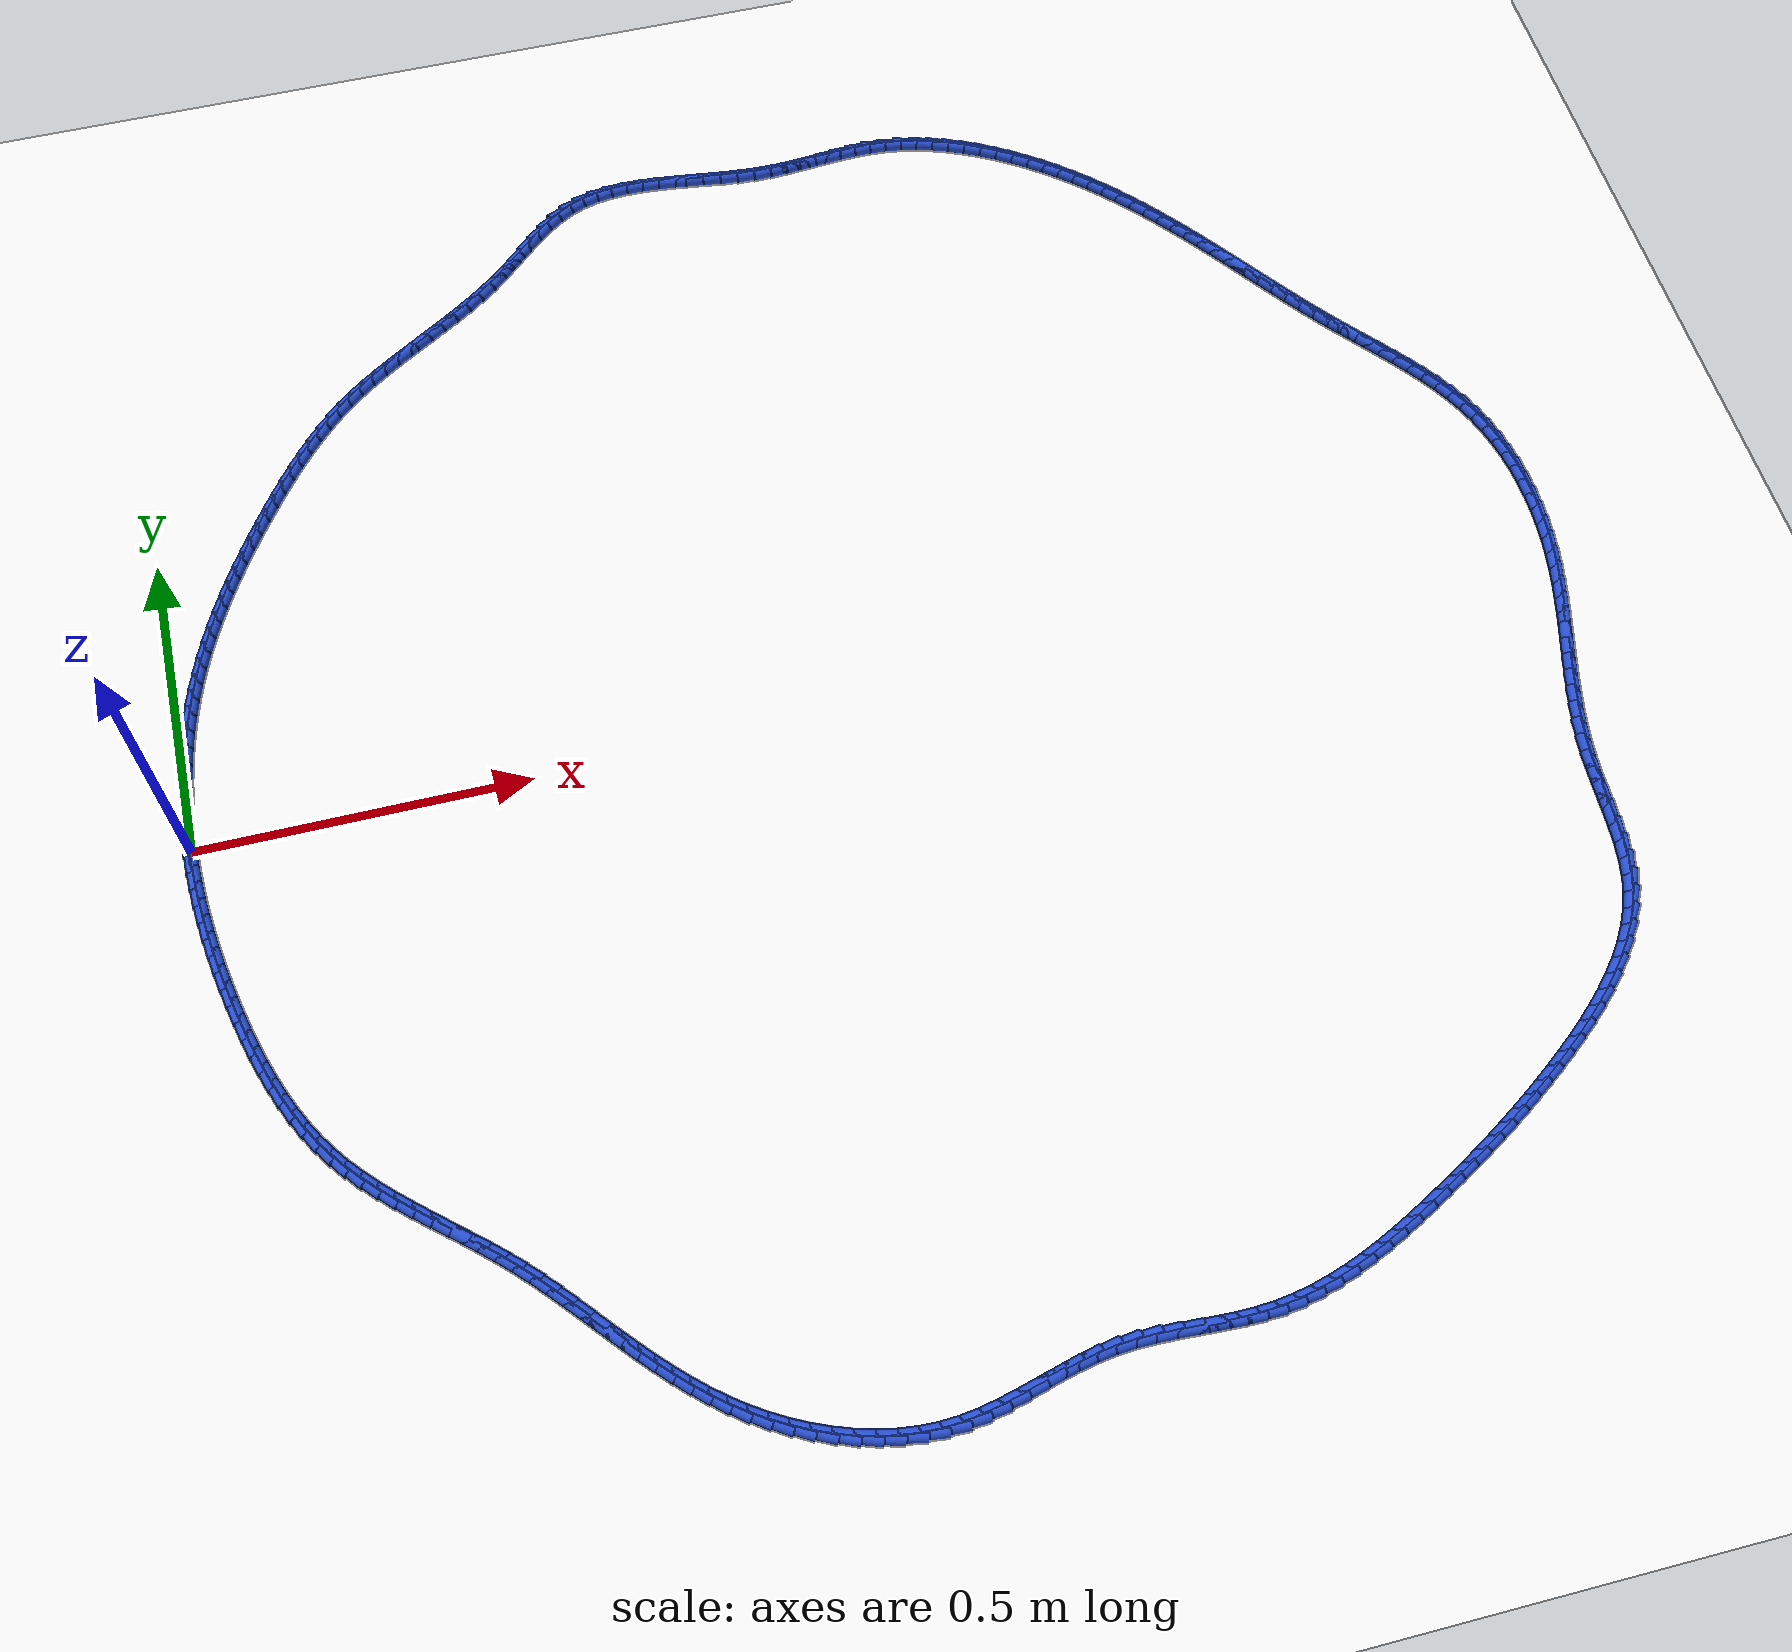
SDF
<sdf version="1.6">
 <world name="default">
  <light name="sun" type="directional">
   <pose>0 0 10 0 -0 0</pose>
   <diffuse>0.8 0.8 0.8 1</diffuse>
   <specular>0.2 0.2 0.2 1</specular>
   <attenuation>
    <range>1000</range>
    <constant>0.9</constant>
    <linear>0.01</linear>
    <quadratic>0.001</quadratic>
   </attenuation>
   <direction>-0.5 0.1 -0.9</direction>
  </light>
  <model name="ground_plane">
   <static>1</static>
   <link name="link">
    <collision name="collision">
     <geometry><plane><normal>0 0 1</normal><size>100 100</size></plane></geometry>
     <surface><friction><ode><mu>100</mu><mu2>50</mu2></ode></friction></surface>
    </collision>
    <visual name="visual">
     <cast_shadows>0</cast_shadows>
     <geometry><plane><normal>0 0 1</normal><size>100 100</size></plane></geometry>
     <material>
      <script><uri>file://media/materials/scripts/gazebo.material</uri><name>Gazebo/WhiteGlow</name></script>
     </material>
    </visual>
   </link>
  </model>
  <gravity>0 0 -9.8</gravity>
  <magnetic_field>6e-06 2.3e-05 -4.2e-05</magnetic_field>
  <atmosphere type="adiabatic"/>
  <physics name="default_physics" default="0" type="ode">
   <max_step_size>0.001</max_step_size>
   <real_time_factor>1</real_time_factor>
   <real_time_update_rate>1000</real_time_update_rate>
  </physics>
  <scene><ambient>0.4 0.4 0.4 1</ambient><background>0.7 0.7 0.7 1</background><shadows>1</shadows></scene>
  <spherical_coordinates>
   <surface_model>EARTH_WGS84</surface_model>
   <latitude_deg>0</latitude_deg>
   <longitude_deg>0</longitude_deg>
   <elevation>0</elevation>
   <heading_deg>0</heading_deg>
  </spherical_coordinates>
  <model name="line">
   <link name="link_0">
    <pose>6.071532165918825e-18 2.7755575615628914e-17 0.01 0 1.57 1.5674756305207604</pose>
    <collision name="collision">
     <geometry><cylinder><radius>0.01</radius><length>0.08</length></cylinder></geometry>
    </collision>
    <visual name="visual">
     <material>
      <script><name>Gazebo/Blue</name><uri>file://media/materials/scripts/gazebo.material</uri></script>
     </material>
     <geometry><cylinder><radius>0.01</radius><length>0.08</length></cylinder></geometry>
    </visual>
   </link>
   <link name="link_1">
    <pose>9.140662447927374e-05 0.027526241773434188 0.01 0 1.57 1.5391433976405038</pose>
    <collision name="collision">
     <geometry><cylinder><radius>0.01</radius><length>0.08</length></cylinder></geometry>
    </collision>
    <visual name="visual">
     <material>
      <script><name>Gazebo/Blue</name><uri>file://media/materials/scripts/gazebo.material</uri></script>
     </material>
     <geometry><cylinder><radius>0.01</radius><length>0.08</length></cylinder></geometry>
    </visual>
   </link>
   <link name="link_2">
    <pose>0.0009641932096115018 0.05509067593601669 0.01 0 1.57 1.5102628457527791</pose>
    <collision name="collision">
     <geometry><cylinder><radius>0.01</radius><length>0.08</length></cylinder></geometry>
    </collision>
    <visual name="visual">
     <material>
      <script><name>Gazebo/Blue</name><uri>file://media/materials/scripts/gazebo.material</uri></script>
     </material>
     <geometry><cylinder><radius>0.01</radius><length>0.08</length></cylinder></geometry>
    </visual>
   </link>
   <link name="link_3">
    <pose>0.0026345334913649883 0.08265062365203125 0.01 0 1.57 1.4807527042488193</pose>
    <collision name="collision">
     <geometry><cylinder><radius>0.01</radius><length>0.08</length></cylinder></geometry>
    </collision>
    <visual name="visual">
     <material>
      <script><name>Gazebo/Blue</name><uri>file://media/materials/scripts/gazebo.material</uri></script>
     </material>
     <geometry><cylinder><radius>0.01</radius><length>0.08</length></cylinder></geometry>
    </visual>
   </link>
   <link name="link_4">
    <pose>0.0051186012057080265 0.1101634060857615 0.01 0 1.57 1.4505329016120636</pose>
    <collision name="collision">
     <geometry><cylinder><radius>0.01</radius><length>0.08</length></cylinder></geometry>
    </collision>
    <visual name="visual">
     <material>
      <script><name>Gazebo/Blue</name><uri>file://media/materials/scripts/gazebo.material</uri></script>
     </material>
     <geometry><cylinder><radius>0.01</radius><length>0.08</length></cylinder></geometry>
    </visual>
   </link>
   <link name="link_5">
    <pose>0.008432570088608916 0.1375863444014912 0.01 0 1.57 1.4195247659248655</pose>
    <collision name="collision">
     <geometry><cylinder><radius>0.01</radius><length>0.08</length></cylinder></geometry>
    </collision>
    <visual name="visual">
     <material>
      <script><name>Gazebo/Blue</name><uri>file://media/materials/scripts/gazebo.material</uri></script>
     </material>
     <geometry><cylinder><radius>0.01</radius><length>0.08</length></cylinder></geometry>
    </visual>
   </link>
   <link name="link_6">
    <pose>0.012592613876035956 0.16487675976350408 0.01 0 1.57 1.3876514010633312</pose>
    <collision name="collision">
     <geometry><cylinder><radius>0.01</radius><length>0.08</length></cylinder></geometry>
    </collision>
    <visual name="visual">
     <material>
      <script><name>Gazebo/Blue</name><uri>file://media/materials/scripts/gazebo.material</uri></script>
     </material>
     <geometry><cylinder><radius>0.01</radius><length>0.08</length></cylinder></geometry>
    </visual>
   </link>
   <link name="link_7">
    <pose>0.01761490630395744 0.1919919733360837 0.01 0 1.57 1.3548382598674122</pose>
    <collision name="collision">
     <geometry><cylinder><radius>0.01</radius><length>0.08</length></cylinder></geometry>
    </collision>
    <visual name="visual">
     <material>
      <script><name>Gazebo/Blue</name><uri>file://media/materials/scripts/gazebo.material</uri></script>
     </material>
     <geometry><cylinder><radius>0.01</radius><length>0.08</length></cylinder></geometry>
    </visual>
   </link>
   <link name="link_8">
    <pose>0.023515621108341656 0.21888930628351383 0.01 0 1.57 1.3210139364723679</pose>
    <collision name="collision">
     <geometry><cylinder><radius>0.01</radius><length>0.08</length></cylinder></geometry>
    </collision>
    <visual name="visual">
     <material>
      <script><name>Gazebo/Blue</name><uri>file://media/materials/scripts/gazebo.material</uri></script>
     </material>
     <geometry><cylinder><radius>0.01</radius><length>0.08</length></cylinder></geometry>
    </visual>
   </link>
   <link name="link_9">
    <pose>0.030310932025156917 0.24552607977007823 0.01 0 1.57 1.286169301168892</pose>
    <collision name="collision">
     <geometry><cylinder><radius>0.01</radius><length>0.08</length></cylinder></geometry>
    </collision>
    <visual name="visual">
     <material>
      <script><name>Gazebo/Blue</name><uri>file://media/materials/scripts/gazebo.material</uri></script>
     </material>
     <geometry><cylinder><radius>0.01</radius><length>0.08</length></cylinder></geometry>
    </visual>
   </link>
   <link name="link_10">
    <pose>0.03801568284108279 0.271860746587741 0.01 0 1.57 1.2516253478246275</pose>
    <collision name="collision">
     <geometry><cylinder><radius>0.01</radius><length>0.08</length></cylinder></geometry>
    </collision>
    <visual name="visual">
     <material>
      <script><name>Gazebo/Blue</name><uri>file://media/materials/scripts/gazebo.material</uri></script>
     </material>
     <geometry><cylinder><radius>0.01</radius><length>0.08</length></cylinder></geometry>
    </visual>
   </link>
   <link name="link_11">
    <pose>0.04661365638157969 0.29787818868918575 0.01 0 1.57 1.2188027455645127</pose>
    <collision name="collision">
     <geometry><cylinder><radius>0.01</radius><length>0.08</length></cylinder></geometry>
    </collision>
    <visual name="visual">
     <material>
      <script><name>Gazebo/Blue</name><uri>file://media/materials/scripts/gazebo.material</uri></script>
     </material>
     <geometry><cylinder><radius>0.01</radius><length>0.08</length></cylinder></geometry>
    </visual>
   </link>
   <link name="link_12">
    <pose>0.05605730993136816 0.3235899423133234 0.01 0 1.57 1.1878201289633987</pose>
    <collision name="collision">
     <geometry><cylinder><radius>0.01</radius><length>0.08</length></cylinder></geometry>
    </collision>
    <visual name="visual">
     <material>
      <script><name>Gazebo/Blue</name><uri>file://media/materials/scripts/gazebo.material</uri></script>
     </material>
     <geometry><cylinder><radius>0.01</radius><length>0.08</length></cylinder></geometry>
    </visual>
   </link>
   <link name="link_13">
    <pose>0.0662977179087826 0.3490087203528622 0.01 0 1.57 1.1587152675533412</pose>
    <collision name="collision">
     <geometry><cylinder><radius>0.01</radius><length>0.08</length></cylinder></geometry>
    </collision>
    <visual name="visual">
     <material>
      <script><name>Gazebo/Blue</name><uri>file://media/materials/scripts/gazebo.material</uri></script>
     </material>
     <geometry><cylinder><radius>0.01</radius><length>0.08</length></cylinder></geometry>
    </visual>
   </link>
   <link name="link_14">
    <pose>0.0772859547321573 0.3741472357005106 0.01 0 1.57 1.1315083457755257</pose>
    <collision name="collision">
     <geometry><cylinder><radius>0.01</radius><length>0.08</length></cylinder></geometry>
    </collision>
    <visual name="visual">
     <material>
      <script><name>Gazebo/Blue</name><uri>file://media/materials/scripts/gazebo.material</uri></script>
     </material>
     <geometry><cylinder><radius>0.01</radius><length>0.08</length></cylinder></geometry>
    </visual>
   </link>
   <link name="link_15">
    <pose>0.08897309481982664 0.3990182012489771 0.01 0 1.57 1.1062049550662587</pose>
    <collision name="collision">
     <geometry><cylinder><radius>0.01</radius><length>0.08</length></cylinder></geometry>
    </collision>
    <visual name="visual">
     <material>
      <script><name>Gazebo/Blue</name><uri>file://media/materials/scripts/gazebo.material</uri></script>
     </material>
     <geometry><cylinder><radius>0.01</radius><length>0.08</length></cylinder></geometry>
    </visual>
   </link>
   <link name="link_16">
    <pose>0.10131021259012496 0.4236343298909699 0.01 0 1.57 1.0827990464568493</pose>
    <collision name="collision">
     <geometry><cylinder><radius>0.01</radius><length>0.08</length></cylinder></geometry>
    </collision>
    <visual name="visual">
     <material>
      <script><name>Gazebo/Blue</name><uri>file://media/materials/scripts/gazebo.material</uri></script>
     </material>
     <geometry><cylinder><radius>0.01</radius><length>0.08</length></cylinder></geometry>
    </visual>
   </link>
   <link name="link_17">
    <pose>0.11424838246138666 0.44800833451919775 0.01 0 1.57 1.0612757265583814</pose>
    <collision name="collision">
     <geometry><cylinder><radius>0.01</radius><length>0.08</length></cylinder></geometry>
    </collision>
    <visual name="visual">
     <material>
      <script><name>Gazebo/Blue</name><uri>file://media/materials/scripts/gazebo.material</uri></script>
     </material>
     <geometry><cylinder><radius>0.01</radius><length>0.08</length></cylinder></geometry>
    </visual>
   </link>
   <link name="link_18">
    <pose>0.127738678851946 0.4721529280263687 0.01 0 1.57 1.0416138213661614</pose>
    <collision name="collision">
     <geometry><cylinder><radius>0.01</radius><length>0.08</length></cylinder></geometry>
    </collision>
    <visual name="visual">
     <material>
      <script><name>Gazebo/Blue</name><uri>file://media/materials/scripts/gazebo.material</uri></script>
     </material>
     <geometry><cylinder><radius>0.01</radius><length>0.08</length></cylinder></geometry>
    </visual>
   </link>
   <link name="link_19">
    <pose>0.1417321761801374 0.4960808233051913 0.01 0 1.57 1.0237881672573892</pose>
    <collision name="collision">
     <geometry><cylinder><radius>0.01</radius><length>0.08</length></cylinder></geometry>
    </collision>
    <visual name="visual">
     <material>
      <script><name>Gazebo/Blue</name><uri>file://media/materials/scripts/gazebo.material</uri></script>
     </material>
     <geometry><cylinder><radius>0.01</radius><length>0.08</length></cylinder></geometry>
    </visual>
   </link>
   <link name="link_20">
    <pose>0.15617994886429518 0.5198047332483741 0.01 0 1.57 1.0077716157572334</pose>
    <collision name="collision">
     <geometry><cylinder><radius>0.01</radius><length>0.08</length></cylinder></geometry>
    </collision>
    <visual name="visual">
     <material>
      <script><name>Gazebo/Blue</name><uri>file://media/materials/scripts/gazebo.material</uri></script>
     </material>
     <geometry><cylinder><radius>0.01</radius><length>0.08</length></cylinder></geometry>
    </visual>
   </link>
   <link name="link_21">
    <pose>0.17103307132275364 0.5433373707486252 0.01 0 1.57 0.99317126619718</pose>
    <collision name="collision">
     <geometry><cylinder><radius>0.01</radius><length>0.08</length></cylinder></geometry>
    </collision>
    <visual name="visual">
     <material>
      <script><name>Gazebo/Blue</name><uri>file://media/materials/scripts/gazebo.material</uri></script>
     </material>
     <geometry><cylinder><radius>0.01</radius><length>0.08</length></cylinder></geometry>
    </visual>
   </link>
   <link name="link_22">
    <pose>0.1862496830895143 0.5666836334216114 0.01 0 1.57 0.9766275970814263</pose>
    <collision name="collision">
     <geometry><cylinder><radius>0.01</radius><length>0.08</length></cylinder></geometry>
    </collision>
    <visual name="visual">
     <material>
      <script><name>Gazebo/Blue</name><uri>file://media/materials/scripts/gazebo.material</uri></script>
     </material>
     <geometry><cylinder><radius>0.01</radius><length>0.08</length></cylinder></geometry>
    </visual>
   </link>
   <link name="link_23">
    <pose>0.20185209193462914 0.5897774373781414 0.01 0 1.57 0.9562866301027767</pose>
    <collision name="collision">
     <geometry><cylinder><radius>0.01</radius><length>0.08</length></cylinder></geometry>
    </collision>
    <visual name="visual">
     <material>
      <script><name>Gazebo/Blue</name><uri>file://media/materials/scripts/gazebo.material</uri></script>
     </material>
     <geometry><cylinder><radius>0.01</radius><length>0.08</length></cylinder></geometry>
    </visual>
   </link>
   <link name="link_24">
    <pose>0.2178968149411595 0.6125148571322007 0.01 0 1.57 0.932014664983601</pose>
    <collision name="collision">
     <geometry><cylinder><radius>0.01</radius><length>0.08</length></cylinder></geometry>
    </collision>
    <visual name="visual">
     <material>
      <script><name>Gazebo/Blue</name><uri>file://media/materials/scripts/gazebo.material</uri></script>
     </material>
     <geometry><cylinder><radius>0.01</radius><length>0.08</length></cylinder></geometry>
    </visual>
   </link>
   <link name="link_25">
    <pose>0.2344406887423353 0.6347916137183387 0.01 0 1.57 0.9036725686274327</pose>
    <collision name="collision">
     <geometry><cylinder><radius>0.01</radius><length>0.08</length></cylinder></geometry>
    </collision>
    <visual name="visual">
     <material>
      <script><name>Gazebo/Blue</name><uri>file://media/materials/scripts/gazebo.material</uri></script>
     </material>
     <geometry><cylinder><radius>0.01</radius><length>0.08</length></cylinder></geometry>
    </visual>
   </link>
   <link name="link_26">
    <pose>0.25154054997138664 0.6565034281711053 0.01 0 1.57 0.8711090639724113</pose>
    <collision name="collision">
     <geometry><cylinder><radius>0.01</radius><length>0.08</length></cylinder></geometry>
    </collision>
    <visual name="visual">
     <material>
      <script><name>Gazebo/Blue</name><uri>file://media/materials/scripts/gazebo.material</uri></script>
     </material>
     <geometry><cylinder><radius>0.01</radius><length>0.08</length></cylinder></geometry>
    </visual>
   </link>
   <link name="link_27">
    <pose>0.2692532352615439 0.6775460215250506 0.01 0 1.57 0.8341738589353659</pose>
    <collision name="collision">
     <geometry><cylinder><radius>0.01</radius><length>0.08</length></cylinder></geometry>
    </collision>
    <visual name="visual">
     <material>
      <script><name>Gazebo/Blue</name><uri>file://media/materials/scripts/gazebo.material</uri></script>
     </material>
     <geometry><cylinder><radius>0.01</radius><length>0.08</length></cylinder></geometry>
    </visual>
   </link>
   <link name="link_28">
    <pose>0.2876355812460367 0.6978151148147239 0.01 0 1.57 0.7927349094634547</pose>
    <collision name="collision">
     <geometry><cylinder><radius>0.01</radius><length>0.08</length></cylinder></geometry>
    </collision>
    <visual name="visual">
     <material>
      <script><name>Gazebo/Blue</name><uri>file://media/materials/scripts/gazebo.material</uri></script>
     </material>
     <geometry><cylinder><radius>0.01</radius><length>0.08</length></cylinder></geometry>
    </visual>
   </link>
   <link name="link_29">
    <pose>0.3067444245580954 0.7172064290746751 0.01 0 1.57 0.7467003768319606</pose>
    <collision name="collision">
     <geometry><cylinder><radius>0.01</radius><length>0.08</length></cylinder></geometry>
    </collision>
    <visual name="visual">
     <material>
      <script><name>Gazebo/Blue</name><uri>file://media/materials/scripts/gazebo.material</uri></script>
     </material>
     <geometry><cylinder><radius>0.01</radius><length>0.08</length></cylinder></geometry>
    </visual>
   </link>
   <link name="link_30">
    <pose>0.32663660183095 0.735615685339454 0.01 0 1.57 0.69765054891539</pose>
    <collision name="collision">
     <geometry><cylinder><radius>0.01</radius><length>0.08</length></cylinder></geometry>
    </collision>
    <visual name="visual">
     <material>
      <script><name>Gazebo/Blue</name><uri>file://media/materials/scripts/gazebo.material</uri></script>
     </material>
     <geometry><cylinder><radius>0.01</radius><length>0.08</length></cylinder></geometry>
    </visual>
   </link>
   <link name="link_31">
    <pose>0.3473459712777182 0.7529759363208088 0.01 0 1.57 0.6540352566464794</pose>
    <collision name="collision">
     <geometry><cylinder><radius>0.01</radius><length>0.08</length></cylinder></geometry>
    </collision>
    <visual name="visual">
     <material>
      <script><name>Gazebo/Blue</name><uri>file://media/materials/scripts/gazebo.material</uri></script>
     </material>
     <geometry><cylinder><radius>0.01</radius><length>0.08</length></cylinder></geometry>
    </visual>
   </link>
   <link name="link_32">
    <pose>0.3687877360080691 0.7694130066442357 0.01 0 1.57 0.6187739888415973</pose>
    <collision name="collision">
     <geometry><cylinder><radius>0.01</radius><length>0.08</length></cylinder></geometry>
    </collision>
    <visual name="visual">
     <material>
      <script><name>Gazebo/Blue</name><uri>file://media/materials/scripts/gazebo.material</uri></script>
     </material>
     <geometry><cylinder><radius>0.01</radius><length>0.08</length></cylinder></geometry>
    </visual>
   </link>
   <link name="link_33">
    <pose>0.390838911848126 0.7851147615514017 0.01 0 1.57 0.5919632500032311</pose>
    <collision name="collision">
     <geometry><cylinder><radius>0.01</radius><length>0.08</length></cylinder></geometry>
    </collision>
    <visual name="visual">
     <material>
      <script><name>Gazebo/Blue</name><uri>file://media/materials/scripts/gazebo.material</uri></script>
     </material>
     <geometry><cylinder><radius>0.01</radius><length>0.08</length></cylinder></geometry>
    </visual>
   </link>
   <link name="link_34">
    <pose>0.41337649636422613 0.8002690959495663 0.01 0 1.57 0.5735818128889433</pose>
    <collision name="collision">
     <geometry><cylinder><radius>0.01</radius><length>0.08</length></cylinder></geometry>
    </collision>
    <visual name="visual">
     <material>
      <script><name>Gazebo/Blue</name><uri>file://media/materials/scripts/gazebo.material</uri></script>
     </material>
     <geometry><cylinder><radius>0.01</radius><length>0.08</length></cylinder></geometry>
    </visual>
   </link>
   <link name="link_35">
    <pose>0.436277487122707 0.8150639047459896 0.01 0 1.57 0.5635497747987276</pose>
    <collision name="collision">
     <geometry><cylinder><radius>0.01</radius><length>0.08</length></cylinder></geometry>
    </collision>
    <visual name="visual">
     <material>
      <script><name>Gazebo/Blue</name><uri>file://media/materials/scripts/gazebo.material</uri></script>
     </material>
     <geometry><cylinder><radius>0.01</radius><length>0.08</length></cylinder></geometry>
    </visual>
   </link>
   <link name="link_36">
    <pose>0.4594188816899058 0.8296870828479308 0.01 0 1.57 0.5617680727313091</pose>
    <collision name="collision">
     <geometry><cylinder><radius>0.01</radius><length>0.08</length></cylinder></geometry>
    </collision>
    <visual name="visual">
     <material>
      <script><name>Gazebo/Blue</name><uri>file://media/materials/scripts/gazebo.material</uri></script>
     </material>
     <geometry><cylinder><radius>0.01</radius><length>0.08</length></cylinder></geometry>
    </visual>
   </link>
   <link name="link_37">
    <pose>0.4826776776321598 0.8443265251626494 0.01 0 1.57 0.5681394617939199</pose>
    <collision name="collision">
     <geometry><cylinder><radius>0.01</radius><length>0.08</length></cylinder></geometry>
    </collision>
    <visual name="visual">
     <material>
      <script><name>Gazebo/Blue</name><uri>file://media/materials/scripts/gazebo.material</uri></script>
     </material>
     <geometry><cylinder><radius>0.01</radius><length>0.08</length></cylinder></geometry>
    </visual>
   </link>
   <link name="link_38">
    <pose>0.5059308725158063 0.8591701265974053 0.01 0 1.57 0.5825720801927277</pose>
    <collision name="collision">
     <geometry><cylinder><radius>0.01</radius><length>0.08</length></cylinder></geometry>
    </collision>
    <visual name="visual">
     <material>
      <script><name>Gazebo/Blue</name><uri>file://media/materials/scripts/gazebo.material</uri></script>
     </material>
     <geometry><cylinder><radius>0.01</radius><length>0.08</length></cylinder></geometry>
    </visual>
   </link>
   <link name="link_39">
    <pose>0.5290554639071826 0.8744057820594578 0.01 0 1.57 0.6049669555885544</pose>
    <collision name="collision">
     <geometry><cylinder><radius>0.01</radius><length>0.08</length></cylinder></geometry>
    </collision>
    <visual name="visual">
     <material>
      <script><name>Gazebo/Blue</name><uri>file://media/materials/scripts/gazebo.material</uri></script>
     </material>
     <geometry><cylinder><radius>0.01</radius><length>0.08</length></cylinder></geometry>
    </visual>
   </link>
   <link name="link_40">
    <pose>0.5519284493726259 0.8902213864560667 0.01 0 1.57 0.6351908210540583</pose>
    <collision name="collision">
     <geometry><cylinder><radius>0.01</radius><length>0.08</length></cylinder></geometry>
    </collision>
    <visual name="visual">
     <material>
      <script><name>Gazebo/Blue</name><uri>file://media/materials/scripts/gazebo.material</uri></script>
     </material>
     <geometry><cylinder><radius>0.01</radius><length>0.08</length></cylinder></geometry>
    </visual>
   </link>
   <link name="link_41">
    <pose>0.5744268264784739 0.9068048346944917 0.01 0 1.57 0.673036185188692</pose>
    <collision name="collision">
     <geometry><cylinder><radius>0.01</radius><length>0.08</length></cylinder></geometry>
    </collision>
    <visual name="visual">
     <material>
      <script><name>Gazebo/Blue</name><uri>file://media/materials/scripts/gazebo.material</uri></script>
     </material>
     <geometry><cylinder><radius>0.01</radius><length>0.08</length></cylinder></geometry>
    </visual>
   </link>
   <link name="link_42">
    <pose>0.5964275927910634 0.924344021681992 0.01 0 1.57 0.717352664158025</pose>
    <collision name="collision">
     <geometry><cylinder><radius>0.01</radius><length>0.08</length></cylinder></geometry>
    </collision>
    <visual name="visual">
     <material>
      <script><name>Gazebo/Blue</name><uri>file://media/materials/scripts/gazebo.material</uri></script>
     </material>
     <geometry><cylinder><radius>0.01</radius><length>0.08</length></cylinder></geometry>
    </visual>
   </link>
   <link name="link_43">
    <pose>0.6178177636820971 0.9430046986432098 0.01 0 1.57 0.7517087414987628</pose>
    <collision name="collision">
     <geometry><cylinder><radius>0.01</radius><length>0.08</length></cylinder></geometry>
    </collision>
    <visual name="visual">
     <material>
      <script><name>Gazebo/Blue</name><uri>file://media/materials/scripts/gazebo.material</uri></script>
     </material>
     <geometry><cylinder><radius>0.01</radius><length>0.08</length></cylinder></geometry>
    </visual>
   </link>
   <link name="link_44">
    <pose>0.6386843173666205 0.9625106124338553 0.01 0 1.57 0.7618939464606381</pose>
    <collision name="collision">
     <geometry><cylinder><radius>0.01</radius><length>0.08</length></cylinder></geometry>
    </collision>
    <visual name="visual">
     <material>
      <script><name>Gazebo/Blue</name><uri>file://media/materials/scripts/gazebo.material</uri></script>
     </material>
     <geometry><cylinder><radius>0.01</radius><length>0.08</length></cylinder></geometry>
    </visual>
   </link>
   <link name="link_45">
    <pose>0.6592986138683352 0.9821779463662619 0.01 0 1.57 0.7474330402225692</pose>
    <collision name="collision">
     <geometry><cylinder><radius>0.01</radius><length>0.08</length></cylinder></geometry>
    </collision>
    <visual name="visual">
     <material>
      <script><name>Gazebo/Blue</name><uri>file://media/materials/scripts/gazebo.material</uri></script>
     </material>
     <geometry><cylinder><radius>0.01</radius><length>0.08</length></cylinder></geometry>
    </visual>
   </link>
   <link name="link_46">
    <pose>0.6799389083792545 1.0013076424485903 0.01 0 1.57 0.7069871632294046</pose>
    <collision name="collision">
     <geometry><cylinder><radius>0.01</radius><length>0.08</length></cylinder></geometry>
    </collision>
    <visual name="visual">
     <material>
      <script><name>Gazebo/Blue</name><uri>file://media/materials/scripts/gazebo.material</uri></script>
     </material>
     <geometry><cylinder><radius>0.01</radius><length>0.08</length></cylinder></geometry>
    </visual>
   </link>
   <link name="link_47">
    <pose>0.7008834560913925 1.0192006426890017 0.01 0 1.57 0.6378870246674813</pose>
    <collision name="collision">
     <geometry><cylinder><radius>0.01</radius><length>0.08</length></cylinder></geometry>
    </collision>
    <visual name="visual">
     <material>
      <script><name>Gazebo/Blue</name><uri>file://media/materials/scripts/gazebo.material</uri></script>
     </material>
     <geometry><cylinder><radius>0.01</radius><length>0.08</length></cylinder></geometry>
    </visual>
   </link>
   <link name="link_48">
    <pose>0.7224105121967626 1.0351578890956572 0.01 0 1.57 0.5367903988083875</pose>
    <collision name="collision">
     <geometry><cylinder><radius>0.01</radius><length>0.08</length></cylinder></geometry>
    </collision>
    <visual name="visual">
     <material>
      <script><name>Gazebo/Blue</name><uri>file://media/materials/scripts/gazebo.material</uri></script>
     </material>
     <geometry><cylinder><radius>0.01</radius><length>0.08</length></cylinder></geometry>
    </visual>
   </link>
   <link name="link_49">
    <pose>0.7447983318873778 1.0484803236767173 0.01 0 1.57 0.4041215997059033</pose>
    <collision name="collision">
     <geometry><cylinder><radius>0.01</radius><length>0.08</length></cylinder></geometry>
    </collision>
    <visual name="visual">
     <material>
      <script><name>Gazebo/Blue</name><uri>file://media/materials/scripts/gazebo.material</uri></script>
     </material>
     <geometry><cylinder><radius>0.01</radius><length>0.08</length></cylinder></geometry>
    </visual>
   </link>
   <link name="link_50">
    <pose>0.7683023593316703 1.058532057928905 0.01 0 1.57 0.2697600171174407</pose>
    <collision name="collision">
     <geometry><cylinder><radius>0.01</radius><length>0.08</length></cylinder></geometry>
    </collision>
    <visual name="visual">
     <material>
      <script><name>Gazebo/Blue</name><uri>file://media/materials/scripts/gazebo.material</uri></script>
     </material>
     <geometry><cylinder><radius>0.01</radius><length>0.08</length></cylinder></geometry>
    </visual>
   </link>
   <link name="link_51">
    <pose>0.7929373839926421 1.065343637040843 0.01 0 1.57 0.15484582065357963</pose>
    <collision name="collision">
     <geometry><cylinder><radius>0.01</radius><length>0.08</length></cylinder></geometry>
    </collision>
    <visual name="visual">
     <material>
      <script><name>Gazebo/Blue</name><uri>file://media/materials/scripts/gazebo.material</uri></script>
     </material>
     <geometry><cylinder><radius>0.01</radius><length>0.08</length></cylinder></geometry>
    </visual>
   </link>
   <link name="link_52">
    <pose>0.8185738375245055 1.0693453694523851 0.01 0 1.57 0.061328003967448606</pose>
    <collision name="collision">
     <geometry><cylinder><radius>0.01</radius><length>0.08</length></cylinder></geometry>
    </collision>
    <visual name="visual">
     <material>
      <script><name>Gazebo/Blue</name><uri>file://media/materials/scripts/gazebo.material</uri></script>
     </material>
     <geometry><cylinder><radius>0.01</radius><length>0.08</length></cylinder></geometry>
    </visual>
   </link>
   <link name="link_53">
    <pose>0.8450801912366201 1.0709729922936573 0.01 0 1.57 -0.011405368272321394</pose>
    <collision name="collision">
     <geometry><cylinder><radius>0.01</radius><length>0.08</length></cylinder></geometry>
    </collision>
    <visual name="visual">
     <material>
      <script><name>Gazebo/Blue</name><uri>file://media/materials/scripts/gazebo.material</uri></script>
     </material>
     <geometry><cylinder><radius>0.01</radius><length>0.08</length></cylinder></geometry>
    </visual>
   </link>
   <link name="link_54">
    <pose>0.8723249164383449 1.0706622426947827 0.01 0 1.57 -0.06501712908490487</pose>
    <collision name="collision">
     <geometry><cylinder><radius>0.01</radius><length>0.08</length></cylinder></geometry>
    </collision>
    <visual name="visual">
     <material>
      <script><name>Gazebo/Blue</name><uri>file://media/materials/scripts/gazebo.material</uri></script>
     </material>
     <geometry><cylinder><radius>0.01</radius><length>0.08</length></cylinder></geometry>
    </visual>
   </link>
   <link name="link_55">
    <pose>0.9001764844390396 1.068848857785887 0.01 0 1.57 -0.10133194038214302</pose>
    <collision name="collision">
     <geometry><cylinder><radius>0.01</radius><length>0.08</length></cylinder></geometry>
    </collision>
    <visual name="visual">
     <material>
      <script><name>Gazebo/Blue</name><uri>file://media/materials/scripts/gazebo.material</uri></script>
     </material>
     <geometry><cylinder><radius>0.01</radius><length>0.08</length></cylinder></geometry>
    </visual>
   </link>
   <link name="link_56">
    <pose>0.9285033665480636 1.0659685746970942 0.01 0 1.57 -0.12186821499923031</pose>
    <collision name="collision">
     <geometry><cylinder><radius>0.01</radius><length>0.08</length></cylinder></geometry>
    </collision>
    <visual name="visual">
     <material>
      <script><name>Gazebo/Blue</name><uri>file://media/materials/scripts/gazebo.material</uri></script>
     </material>
     <geometry><cylinder><radius>0.01</radius><length>0.08</length></cylinder></geometry>
    </visual>
   </link>
   <link name="link_57">
    <pose>0.9571740340747757 1.0624571305585282 0.01 0 1.57 -0.12764338985851886</pose>
    <collision name="collision">
     <geometry><cylinder><radius>0.01</radius><length>0.08</length></cylinder></geometry>
    </collision>
    <visual name="visual">
     <material>
      <script><name>Gazebo/Blue</name><uri>file://media/materials/scripts/gazebo.material</uri></script>
     </material>
     <geometry><cylinder><radius>0.01</radius><length>0.08</length></cylinder></geometry>
    </visual>
   </link>
   <link name="link_58">
    <pose>0.9860569583285361 1.0587502625003142 0.01 0 1.57 -0.11911975180306798</pose>
    <collision name="collision">
     <geometry><cylinder><radius>0.01</radius><length>0.08</length></cylinder></geometry>
    </collision>
    <visual name="visual">
     <material>
      <script><name>Gazebo/Blue</name><uri>file://media/materials/scripts/gazebo.material</uri></script>
     </material>
     <geometry><cylinder><radius>0.01</radius><length>0.08</length></cylinder></geometry>
    </visual>
   </link>
   <link name="link_59">
    <pose>1.0150206106187034 1.0552837076525767 0.01 0 1.57 -0.09621631643686032</pose>
    <collision name="collision">
     <geometry><cylinder><radius>0.01</radius><length>0.08</length></cylinder></geometry>
    </collision>
    <visual name="visual">
     <material>
      <script><name>Gazebo/Blue</name><uri>file://media/materials/scripts/gazebo.material</uri></script>
     </material>
     <geometry><cylinder><radius>0.01</radius><length>0.08</length></cylinder></geometry>
    </visual>
   </link>
   <link name="link_60">
    <pose>1.0439334622546377 1.05249320314544 0.01 0 1.57 -0.05836338524251697</pose>
    <collision name="collision">
     <geometry><cylinder><radius>0.01</radius><length>0.08</length></cylinder></geometry>
    </collision>
    <visual name="visual">
     <material>
      <script><name>Gazebo/Blue</name><uri>file://media/materials/scripts/gazebo.material</uri></script>
     </material>
     <geometry><cylinder><radius>0.01</radius><length>0.08</length></cylinder></geometry>
    </visual>
   </link>
   <link name="link_61">
    <pose>1.0726639845456978 1.0508144861090285 0.01 0 1.57 -0.005816245046619494</pose>
    <collision name="collision">
     <geometry><cylinder><radius>0.01</radius><length>0.08</length></cylinder></geometry>
    </collision>
    <visual name="visual">
     <material>
      <script><name>Gazebo/Blue</name><uri>file://media/materials/scripts/gazebo.material</uri></script>
     </material>
     <geometry><cylinder><radius>0.01</radius><length>0.08</length></cylinder></geometry>
    </visual>
   </link>
   <link name="link_62">
    <pose>1.1010866167589104 1.050649171251073 0.01 0 1.57 0.04379226199682296</pose>
    <collision name="collision">
     <geometry><cylinder><radius>0.01</radius><length>0.08</length></cylinder></geometry>
    </collision>
    <visual name="visual">
     <material>
      <script><name>Gazebo/Blue</name><uri>file://media/materials/scripts/gazebo.material</uri></script>
     </material>
     <geometry><cylinder><radius>0.01</radius><length>0.08</length></cylinder></geometry>
    </visual>
   </link>
   <link name="link_63">
    <pose>1.1291666104742513 1.0518796443782632 0.01 0 1.57 0.07562860127090518</pose>
    <collision name="collision">
     <geometry><cylinder><radius>0.01</radius><length>0.08</length></cylinder></geometry>
    </collision>
    <visual name="visual">
     <material>
      <script><name>Gazebo/Blue</name><uri>file://media/materials/scripts/gazebo.material</uri></script>
     </material>
     <geometry><cylinder><radius>0.01</radius><length>0.08</length></cylinder></geometry>
    </visual>
   </link>
   <link name="link_64">
    <pose>1.1569399072762656 1.0539841137998145 0.01 0 1.57 0.08869842491510196</pose>
    <collision name="collision">
     <geometry><cylinder><radius>0.01</radius><length>0.08</length></cylinder></geometry>
    </collision>
    <visual name="visual">
     <material>
      <script><name>Gazebo/Blue</name><uri>file://media/materials/scripts/gazebo.material</uri></script>
     </material>
     <geometry><cylinder><radius>0.01</radius><length>0.08</length></cylinder></geometry>
    </visual>
   </link>
   <link name="link_65">
    <pose>1.1844443129211908 1.0564301292282445 0.01 0 1.57 0.08249794219095717</pose>
    <collision name="collision">
     <geometry><cylinder><radius>0.01</radius><length>0.08</length></cylinder></geometry>
    </collision>
    <visual name="visual">
     <material>
      <script><name>Gazebo/Blue</name><uri>file://media/materials/scripts/gazebo.material</uri></script>
     </material>
     <geometry><cylinder><radius>0.01</radius><length>0.08</length></cylinder></geometry>
    </visual>
   </link>
   <link name="link_66">
    <pose>1.2117176331652648 1.0586852403760707 0.01 0 1.57 0.056503833117821985</pose>
    <collision name="collision">
     <geometry><cylinder><radius>0.01</radius><length>0.08</length></cylinder></geometry>
    </collision>
    <visual name="visual">
     <material>
      <script><name>Gazebo/Blue</name><uri>file://media/materials/scripts/gazebo.material</uri></script>
     </material>
     <geometry><cylinder><radius>0.01</radius><length>0.08</length></cylinder></geometry>
    </visual>
   </link>
   <link name="link_67">
    <pose>1.2387976737647237 1.0602169969558104 0.01 0 1.57 0.010248709494177286</pose>
    <collision name="collision">
     <geometry><cylinder><radius>0.01</radius><length>0.08</length></cylinder></geometry>
    </collision>
    <visual name="visual">
     <material>
      <script><name>Gazebo/Blue</name><uri>file://media/materials/scripts/gazebo.material</uri></script>
     </material>
     <geometry><cylinder><radius>0.01</radius><length>0.08</length></cylinder></geometry>
    </visual>
   </link>
   <link name="link_68">
    <pose>1.2657222404758064 1.0604929486799826 0.01 0 1.57 -0.05632960257344808</pose>
    <collision name="collision">
     <geometry><cylinder><radius>0.01</radius><length>0.08</length></cylinder></geometry>
    </collision>
    <visual name="visual">
     <material>
      <script><name>Gazebo/Blue</name><uri>file://media/materials/scripts/gazebo.material</uri></script>
     </material>
     <geometry><cylinder><radius>0.01</radius><length>0.08</length></cylinder></geometry>
    </visual>
   </link>
   <link name="link_69">
    <pose>1.2925290333305801 1.0589813335568157 0.01 0 1.57 -0.13575664744811794</pose>
    <collision name="collision">
     <geometry><cylinder><radius>0.01</radius><length>0.08</length></cylinder></geometry>
    </collision>
    <visual name="visual">
     <material>
      <script><name>Gazebo/Blue</name><uri>file://media/materials/scripts/gazebo.material</uri></script>
     </material>
     <geometry><cylinder><radius>0.01</radius><length>0.08</length></cylinder></geometry>
    </visual>
   </link>
   <link name="link_70">
    <pose>1.3192274863995046 1.055334409391231 0.01 0 1.57 -0.2115682908477505</pose>
    <collision name="collision">
     <geometry><cylinder><radius>0.01</radius><length>0.08</length></cylinder></geometry>
    </collision>
    <visual name="visual">
     <material>
      <script><name>Gazebo/Blue</name><uri>file://media/materials/scripts/gazebo.material</uri></script>
     </material>
     <geometry><cylinder><radius>0.01</radius><length>0.08</length></cylinder></geometry>
    </visual>
   </link>
   <link name="link_71">
    <pose>1.3457608187836796 1.0496355130849007 0.01 0 1.57 -0.2814968620393931</pose>
    <collision name="collision">
     <geometry><cylinder><radius>0.01</radius><length>0.08</length></cylinder></geometry>
    </collision>
    <visual name="visual">
     <material>
      <script><name>Gazebo/Blue</name><uri>file://media/materials/scripts/gazebo.material</uri></script>
     </material>
     <geometry><cylinder><radius>0.01</radius><length>0.08</length></cylinder></geometry>
    </visual>
   </link>
   <link name="link_72">
    <pose>1.3720627808383283 1.0420296258845778 0.01 0 1.57 -0.34577118275028335</pose>
    <collision name="collision">
     <geometry><cylinder><radius>0.01</radius><length>0.08</length></cylinder></geometry>
    </collision>
    <visual name="visual">
     <material>
      <script><name>Gazebo/Blue</name><uri>file://media/materials/scripts/gazebo.material</uri></script>
     </material>
     <geometry><cylinder><radius>0.01</radius><length>0.08</length></cylinder></geometry>
    </visual>
   </link>
   <link name="link_73">
    <pose>1.3980671229186736 1.0326617290370155 0.01 0 1.57 -0.4047649698173029</pose>
    <collision name="collision">
     <geometry><cylinder><radius>0.01</radius><length>0.08</length></cylinder></geometry>
    </collision>
    <visual name="visual">
     <material>
      <script><name>Gazebo/Blue</name><uri>file://media/materials/scripts/gazebo.material</uri></script>
     </material>
     <geometry><cylinder><radius>0.01</radius><length>0.08</length></cylinder></geometry>
    </visual>
   </link>
   <link name="link_74">
    <pose>1.423707595379938 1.0216768037889663 0.01 0 1.57 -0.4589335959532262</pose>
    <collision name="collision">
     <geometry><cylinder><radius>0.01</radius><length>0.08</length></cylinder></geometry>
    </collision>
    <visual name="visual">
     <material>
      <script><name>Gazebo/Blue</name><uri>file://media/materials/scripts/gazebo.material</uri></script>
     </material>
     <geometry><cylinder><radius>0.01</radius><length>0.08</length></cylinder></geometry>
    </visual>
   </link>
   <link name="link_75">
    <pose>1.4489179485773436 1.0092198313871834 0.01 0 1.57 -0.5087680752783025</pose>
    <collision name="collision">
     <geometry><cylinder><radius>0.01</radius><length>0.08</length></cylinder></geometry>
    </collision>
    <visual name="visual">
     <material>
      <script><name>Gazebo/Blue</name><uri>file://media/materials/scripts/gazebo.material</uri></script>
     </material>
     <geometry><cylinder><radius>0.01</radius><length>0.08</length></cylinder></geometry>
    </visual>
   </link>
   <link name="link_76">
    <pose>1.4736319328661136 0.9954357930784198 0.01 0 1.57 -0.5547646862628934</pose>
    <collision name="collision">
     <geometry><cylinder><radius>0.01</radius><length>0.08</length></cylinder></geometry>
    </collision>
    <visual name="visual">
     <material>
      <script><name>Gazebo/Blue</name><uri>file://media/materials/scripts/gazebo.material</uri></script>
     </material>
     <geometry><cylinder><radius>0.01</radius><length>0.08</length></cylinder></geometry>
    </visual>
   </link>
   <link name="link_77">
    <pose>1.49778329860147 0.980469670109428 0.01 0 1.57 -0.5974070934406732</pose>
    <collision name="collision">
     <geometry><cylinder><radius>0.01</radius><length>0.08</length></cylinder></geometry>
    </collision>
    <visual name="visual">
     <material>
      <script><name>Gazebo/Blue</name><uri>file://media/materials/scripts/gazebo.material</uri></script>
     </material>
     <geometry><cylinder><radius>0.01</radius><length>0.08</length></cylinder></geometry>
    </visual>
   </link>
   <link name="link_78">
    <pose>1.5213057961386367 0.9644664437269611 0.01 0 1.57 -0.6371577218860998</pose>
    <collision name="collision">
     <geometry><cylinder><radius>0.01</radius><length>0.08</length></cylinder></geometry>
    </collision>
    <visual name="visual">
     <material>
      <script><name>Gazebo/Blue</name><uri>file://media/materials/scripts/gazebo.material</uri></script>
     </material>
     <geometry><cylinder><radius>0.01</radius><length>0.08</length></cylinder></geometry>
    </visual>
   </link>
   <link name="link_79">
    <pose>1.544133175832835 0.947571095177772 0.01 0 1.57 -0.6744556936210766</pose>
    <collision name="collision">
     <geometry><cylinder><radius>0.01</radius><length>0.08</length></cylinder></geometry>
    </collision>
    <visual name="visual">
     <material>
      <script><name>Gazebo/Blue</name><uri>file://media/materials/scripts/gazebo.material</uri></script>
     </material>
     <geometry><cylinder><radius>0.01</radius><length>0.08</length></cylinder></geometry>
    </visual>
   </link>
   <link name="link_80">
    <pose>1.5661991880434134 0.9299286057051075 0.01 0 1.57 -0.7097141701352017</pose>
    <collision name="collision">
     <geometry><cylinder><radius>0.01</radius><length>0.08</length></cylinder></geometry>
    </collision>
    <visual name="visual">
     <material>
      <script><name>Gazebo/Blue</name><uri>file://media/materials/scripts/gazebo.material</uri></script>
     </material>
     <geometry><cylinder><radius>0.01</radius><length>0.08</length></cylinder></geometry>
    </visual>
   </link>
   <link name="link_81">
    <pose>1.5874584140493833 0.911666254750063 0.01 0 1.57 -0.7430870660620886</pose>
    <collision name="collision">
     <geometry><cylinder><radius>0.01</radius><length>0.08</length></cylinder></geometry>
    </collision>
    <visual name="visual">
     <material>
      <script><name>Gazebo/Blue</name><uri>file://media/materials/scripts/gazebo.material</uri></script>
     </material>
     <geometry><cylinder><radius>0.01</radius><length>0.08</length></cylinder></geometry>
    </visual>
   </link>
   <link name="link_82">
    <pose>1.6079473060088687 0.8928417491123195 0.01 0 1.57 -0.7744306908484367</pose>
    <collision name="collision">
     <geometry><cylinder><radius>0.01</radius><length>0.08</length></cylinder></geometry>
    </collision>
    <visual name="visual">
     <material>
      <script><name>Gazebo/Blue</name><uri>file://media/materials/scripts/gazebo.material</uri></script>
     </material>
     <geometry><cylinder><radius>0.01</radius><length>0.08</length></cylinder></geometry>
    </visual>
   </link>
   <link name="link_83">
    <pose>1.6277224269105048 0.873495705710334 0.01 0 1.57 -0.8036026909010632</pose>
    <collision name="collision">
     <geometry><cylinder><radius>0.01</radius><length>0.08</length></cylinder></geometry>
    </collision>
    <visual name="visual">
     <material>
      <script><name>Gazebo/Blue</name><uri>file://media/materials/scripts/gazebo.material</uri></script>
     </material>
     <geometry><cylinder><radius>0.01</radius><length>0.08</length></cylinder></geometry>
    </visual>
   </link>
   <link name="link_84">
    <pose>1.6468403397429277 0.8536687414625633 0.01 0 1.57 -0.8304886669749341</pose>
    <collision name="collision">
     <geometry><cylinder><radius>0.01</radius><length>0.08</length></cylinder></geometry>
    </collision>
    <visual name="visual">
     <material>
      <script><name>Gazebo/Blue</name><uri>file://media/materials/scripts/gazebo.material</uri></script>
     </material>
     <geometry><cylinder><radius>0.01</radius><length>0.08</length></cylinder></geometry>
    </visual>
   </link>
   <link name="link_85">
    <pose>1.6653576074947722 0.8334014732874644 0.01 0 1.57 -0.8549998306771901</pose>
    <collision name="collision">
     <geometry><cylinder><radius>0.01</radius><length>0.08</length></cylinder></geometry>
    </collision>
    <visual name="visual">
     <material>
      <script><name>Gazebo/Blue</name><uri>file://media/materials/scripts/gazebo.material</uri></script>
     </material>
     <geometry><cylinder><radius>0.01</radius><length>0.08</length></cylinder></geometry>
    </visual>
   </link>
   <link name="link_86">
    <pose>1.683330793154674 0.8127345181034947 0.01 0 1.57 -0.8770699544317554</pose>
    <collision name="collision">
     <geometry><cylinder><radius>0.01</radius><length>0.08</length></cylinder></geometry>
    </collision>
    <visual name="visual">
     <material>
      <script><name>Gazebo/Blue</name><uri>file://media/materials/scripts/gazebo.material</uri></script>
     </material>
     <geometry><cylinder><radius>0.01</radius><length>0.08</length></cylinder></geometry>
    </visual>
   </link>
   <link name="link_87">
    <pose>1.7008164597112685 0.791708492829111 0.01 0 1.57 -0.896651936687607</pose>
    <collision name="collision">
     <geometry><cylinder><radius>0.01</radius><length>0.08</length></cylinder></geometry>
    </collision>
    <visual name="visual">
     <material>
      <script><name>Gazebo/Blue</name><uri>file://media/materials/scripts/gazebo.material</uri></script>
     </material>
     <geometry><cylinder><radius>0.01</radius><length>0.08</length></cylinder></geometry>
    </visual>
   </link>
   <link name="link_88">
    <pose>1.717871170153192 0.7703640143827708 0.01 0 1.57 -0.9137142592741855</pose>
    <collision name="collision">
     <geometry><cylinder><radius>0.01</radius><length>0.08</length></cylinder></geometry>
    </collision>
    <visual name="visual">
     <material>
      <script><name>Gazebo/Blue</name><uri>file://media/materials/scripts/gazebo.material</uri></script>
     </material>
     <geometry><cylinder><radius>0.01</radius><length>0.08</length></cylinder></geometry>
    </visual>
   </link>
   <link name="link_89">
    <pose>1.7345514874690784 0.7487416996829299 0.01 0 1.57 -0.928211896223714</pose>
    <collision name="collision">
     <geometry><cylinder><radius>0.01</radius><length>0.08</length></cylinder></geometry>
    </collision>
    <visual name="visual">
     <material>
      <script><name>Gazebo/Blue</name><uri>file://media/materials/scripts/gazebo.material</uri></script>
     </material>
     <geometry><cylinder><radius>0.01</radius><length>0.08</length></cylinder></geometry>
    </visual>
   </link>
   <link name="link_90">
    <pose>1.750914754425457 0.7268822931563974 0.01 0 1.57 -0.9398255759516793</pose>
    <collision name="collision">
     <geometry><cylinder><radius>0.01</radius><length>0.08</length></cylinder></geometry>
    </collision>
    <visual name="visual">
     <material>
      <script><name>Gazebo/Blue</name><uri>file://media/materials/scripts/gazebo.material</uri></script>
     </material>
     <geometry><cylinder><radius>0.01</radius><length>0.08</length></cylinder></geometry>
    </visual>
   </link>
   <link name="link_91">
    <pose>1.7670276321875196 0.7048280629634093 0.01 0 1.57 -0.948343360154536</pose>
    <collision name="collision">
     <geometry><cylinder><radius>0.01</radius><length>0.08</length></cylinder></geometry>
    </collision>
    <visual name="visual">
     <material>
      <script><name>Gazebo/Blue</name><uri>file://media/materials/scripts/gazebo.material</uri></script>
     </material>
     <geometry><cylinder><radius>0.01</radius><length>0.08</length></cylinder></geometry>
    </visual>
   </link>
   <link name="link_92">
    <pose>1.782962916383738 0.6826222803643174 0.01 0 1.57 -0.9537593527931839</pose>
    <collision name="collision">
     <geometry><cylinder><radius>0.01</radius><length>0.08</length></cylinder></geometry>
    </collision>
    <visual name="visual">
     <material>
      <script><name>Gazebo/Blue</name><uri>file://media/materials/scripts/gazebo.material</uri></script>
     </material>
     <geometry><cylinder><radius>0.01</radius><length>0.08</length></cylinder></geometry>
    </visual>
   </link>
   <link name="link_93">
    <pose>1.7987935105352801 0.660308234261958 0.01 0 1.57 -0.9560781474358409</pose>
    <collision name="collision">
     <geometry><cylinder><radius>0.01</radius><length>0.08</length></cylinder></geometry>
    </collision>
    <visual name="visual">
     <material>
      <script><name>Gazebo/Blue</name><uri>file://media/materials/scripts/gazebo.material</uri></script>
     </material>
     <geometry><cylinder><radius>0.01</radius><length>0.08</length></cylinder></geometry>
    </visual>
   </link>
   <link name="link_94">
    <pose>1.8145923181633117 0.637929213559168 0.01 0 1.57 -0.9553096771093699</pose>
    <collision name="collision">
     <geometry><cylinder><radius>0.01</radius><length>0.08</length></cylinder></geometry>
    </collision>
    <visual name="visual">
     <material>
      <script><name>Gazebo/Blue</name><uri>file://media/materials/scripts/gazebo.material</uri></script>
     </material>
     <geometry><cylinder><radius>0.01</radius><length>0.08</length></cylinder></geometry>
    </visual>
   </link>
   <link name="link_95">
    <pose>1.8304322427890003 0.6155285071587838 0.01 0 1.57 -0.9514684917912469</pose>
    <collision name="collision">
     <geometry><cylinder><radius>0.01</radius><length>0.08</length></cylinder></geometry>
    </collision>
    <visual name="visual">
     <material>
      <script><name>Gazebo/Blue</name><uri>file://media/materials/scripts/gazebo.material</uri></script>
     </material>
     <geometry><cylinder><radius>0.01</radius><length>0.08</length></cylinder></geometry>
    </visual>
   </link>
   <link name="link_96">
    <pose>1.8463861879335124 0.5931494039636414 0.01 0 1.57 -0.944573902057694</pose>
    <collision name="collision">
     <geometry><cylinder><radius>0.01</radius><length>0.08</length></cylinder></geometry>
    </collision>
    <visual name="visual">
     <material>
      <script><name>Gazebo/Blue</name><uri>file://media/materials/scripts/gazebo.material</uri></script>
     </material>
     <geometry><cylinder><radius>0.01</radius><length>0.08</length></cylinder></geometry>
    </visual>
   </link>
   <link name="link_97">
    <pose>1.8625270571180146 0.5708351928765777 0.01 0 1.57 -0.9346509581187428</pose>
    <collision name="collision">
     <geometry><cylinder><radius>0.01</radius><length>0.08</length></cylinder></geometry>
    </collision>
    <visual name="visual">
     <material>
      <script><name>Gazebo/Blue</name><uri>file://media/materials/scripts/gazebo.material</uri></script>
     </material>
     <geometry><cylinder><radius>0.01</radius><length>0.08</length></cylinder></geometry>
    </visual>
   </link>
   <link name="link_98">
    <pose>1.8789277538636748 0.5486291628004295 0.01 0 1.57 -0.9217322134387544</pose>
    <collision name="collision">
     <geometry><cylinder><radius>0.01</radius><length>0.08</length></cylinder></geometry>
    </collision>
    <visual name="visual">
     <material>
      <script><name>Gazebo/Blue</name><uri>file://media/materials/scripts/gazebo.material</uri></script>
     </material>
     <geometry><cylinder><radius>0.01</radius><length>0.08</length></cylinder></geometry>
    </visual>
   </link>
   <link name="link_99">
    <pose>1.8956611816916582 0.5265746026380322 0.01 0 1.57 -0.9058967996957161</pose>
    <collision name="collision">
     <geometry><cylinder><radius>0.01</radius><length>0.08</length></cylinder></geometry>
    </collision>
    <visual name="visual">
     <material>
      <script><name>Gazebo/Blue</name><uri>file://media/materials/scripts/gazebo.material</uri></script>
     </material>
     <geometry><cylinder><radius>0.01</radius><length>0.08</length></cylinder></geometry>
    </visual>
   </link>
   <link name="link_100">
    <pose>1.9127993201695321 0.5047143318786717 0.01 0 1.57 -0.8911269112037871</pose>
    <collision name="collision">
     <geometry><cylinder><radius>0.01</radius><length>0.08</length></cylinder></geometry>
    </collision>
    <visual name="visual">
     <material>
      <script><name>Gazebo/Blue</name><uri>file://media/materials/scripts/gazebo.material</uri></script>
     </material>
     <geometry><cylinder><radius>0.01</radius><length>0.08</length></cylinder></geometry>
    </visual>
   </link>
   <link name="link_101">
    <pose>1.9303143074345932 0.4830404456892115 0.01 0 1.57 -0.884762328135932</pose>
    <collision name="collision">
     <geometry><cylinder><radius>0.01</radius><length>0.08</length></cylinder></geometry>
    </collision>
    <visual name="visual">
     <material>
      <script><name>Gazebo/Blue</name><uri>file://media/materials/scripts/gazebo.material</uri></script>
     </material>
     <geometry><cylinder><radius>0.01</radius><length>0.08</length></cylinder></geometry>
    </visual>
   </link>
   <link name="link_102">
    <pose>1.947990494550314 0.46144963423226376 0.01 0 1.57 -0.8875484873435319</pose>
    <collision name="collision">
     <geometry><cylinder><radius>0.01</radius><length>0.08</length></cylinder></geometry>
    </collision>
    <visual name="visual">
     <material>
      <script><name>Gazebo/Blue</name><uri>file://media/materials/scripts/gazebo.material</uri></script>
     </material>
     <geometry><cylinder><radius>0.01</radius><length>0.08</length></cylinder></geometry>
    </visual>
   </link>
   <link name="link_103">
    <pose>1.9655914872995524 0.43982804805477455 0.01 0 1.57 -0.8995264937181116</pose>
    <collision name="collision">
     <geometry><cylinder><radius>0.01</radius><length>0.08</length></cylinder></geometry>
    </collision>
    <visual name="visual">
     <material>
      <script><name>Gazebo/Blue</name><uri>file://media/materials/scripts/gazebo.material</uri></script>
     </material>
     <geometry><cylinder><radius>0.01</radius><length>0.08</length></cylinder></geometry>
    </visual>
   </link>
   <link name="link_104">
    <pose>1.982880891465168 0.4180618377036901 0.01 0 1.57 -0.9208492822064647</pose>
    <collision name="collision">
     <geometry><cylinder><radius>0.01</radius><length>0.08</length></cylinder></geometry>
    </collision>
    <visual name="visual">
     <material>
      <script><name>Gazebo/Blue</name><uri>file://media/materials/scripts/gazebo.material</uri></script>
     </material>
     <geometry><cylinder><radius>0.01</radius><length>0.08</length></cylinder></geometry>
    </visual>
   </link>
   <link name="link_105">
    <pose>1.9996223128300206 0.3960371537259576 0.01 0 1.57 -0.9517546509273949</pose>
    <collision name="collision">
     <geometry><cylinder><radius>0.01</radius><length>0.08</length></cylinder></geometry>
    </collision>
    <visual name="visual">
     <material>
      <script><name>Gazebo/Blue</name><uri>file://media/materials/scripts/gazebo.material</uri></script>
     </material>
     <geometry><cylinder><radius>0.01</radius><length>0.08</length></cylinder></geometry>
    </visual>
   </link>
   <link name="link_106">
    <pose>2.015579357176968 0.37364014666852324 0.01 0 1.57 -0.9925124548067706</pose>
    <collision name="collision">
     <geometry><cylinder><radius>0.01</radius><length>0.08</length></cylinder></geometry>
    </collision>
    <visual name="visual">
     <material>
      <script><name>Gazebo/Blue</name><uri>file://media/materials/scripts/gazebo.material</uri></script>
     </material>
     <geometry><cylinder><radius>0.01</radius><length>0.08</length></cylinder></geometry>
    </visual>
   </link>
   <link name="link_107">
    <pose>2.0305156302888716 0.35075696707833376 0.01 0 1.57 -1.0433393270357874</pose>
    <collision name="collision">
     <geometry><cylinder><radius>0.01</radius><length>0.08</length></cylinder></geometry>
    </collision>
    <visual name="visual">
     <material>
      <script><name>Gazebo/Blue</name><uri>file://media/materials/scripts/gazebo.material</uri></script>
     </material>
     <geometry><cylinder><radius>0.01</radius><length>0.08</length></cylinder></geometry>
    </visual>
   </link>
   <link name="link_108">
    <pose>2.04419473794859 0.32727376550233517 0.01 0 1.57 -1.1042760970246959</pose>
    <collision name="collision">
     <geometry><cylinder><radius>0.01</radius><length>0.08</length></cylinder></geometry>
    </collision>
    <visual name="visual">
     <material>
      <script><name>Gazebo/Blue</name><uri>file://media/materials/scripts/gazebo.material</uri></script>
     </material>
     <geometry><cylinder><radius>0.01</radius><length>0.08</length></cylinder></geometry>
    </visual>
   </link>
   <link name="link_109">
    <pose>2.0563802859389813 0.30307669248747465 0.01 0 1.57 -1.1745984188050587</pose>
    <collision name="collision">
     <geometry><cylinder><radius>0.01</radius><length>0.08</length></cylinder></geometry>
    </collision>
    <visual name="visual">
     <material>
      <script><name>Gazebo/Blue</name><uri>file://media/materials/scripts/gazebo.material</uri></script>
     </material>
     <geometry><cylinder><radius>0.01</radius><length>0.08</length></cylinder></geometry>
    </visual>
   </link>
   <link name="link_110">
    <pose>2.0668455844285476 0.27805916511225565 0.01 0 1.57 -1.2464943645264446</pose>
    <collision name="collision">
     <geometry><cylinder><radius>0.01</radius><length>0.08</length></cylinder></geometry>
    </collision>
    <visual name="visual">
     <material>
      <script><name>Gazebo/Blue</name><uri>file://media/materials/scripts/gazebo.material</uri></script>
     </material>
     <geometry><cylinder><radius>0.01</radius><length>0.08</length></cylinder></geometry>
    </visual>
   </link>
   <link name="link_111">
    <pose>2.075526473464767 0.2522363009458885 0.01 0 1.57 -1.3138248428905526</pose>
    <collision name="collision">
     <geometry><cylinder><radius>0.01</radius><length>0.08</length></cylinder></geometry>
    </collision>
    <visual name="visual">
     <material>
      <script><name>Gazebo/Blue</name><uri>file://media/materials/scripts/gazebo.material</uri></script>
     </material>
     <geometry><cylinder><radius>0.01</radius><length>0.08</length></cylinder></geometry>
    </visual>
   </link>
   <link name="link_112">
    <pose>2.082493406678267 0.22572401464934205 0.01 0 1.57 -1.3765647534082033</pose>
    <collision name="collision">
     <geometry><cylinder><radius>0.01</radius><length>0.08</length></cylinder></geometry>
    </collision>
    <visual name="visual">
     <material>
      <script><name>Gazebo/Blue</name><uri>file://media/materials/scripts/gazebo.material</uri></script>
     </material>
     <geometry><cylinder><radius>0.01</radius><length>0.08</length></cylinder></geometry>
    </visual>
   </link>
   <link name="link_113">
    <pose>2.0878208965937883 0.19864126013648187 0.01 0 1.57 -1.4349874410340602</pose>
    <collision name="collision">
     <geometry><cylinder><radius>0.01</radius><length>0.08</length></cylinder></geometry>
    </collision>
    <visual name="visual">
     <material>
      <script><name>Gazebo/Blue</name><uri>file://media/materials/scripts/gazebo.material</uri></script>
     </material>
     <geometry><cylinder><radius>0.01</radius><length>0.08</length></cylinder></geometry>
    </visual>
   </link>
   <link name="link_114">
    <pose>2.09158345573607 0.17110699132117219 0.01 0 1.57 -1.48944061346914</pose>
    <collision name="collision">
     <geometry><cylinder><radius>0.01</radius><length>0.08</length></cylinder></geometry>
    </collision>
    <visual name="visual">
     <material>
      <script><name>Gazebo/Blue</name><uri>file://media/materials/scripts/gazebo.material</uri></script>
     </material>
     <geometry><cylinder><radius>0.01</radius><length>0.08</length></cylinder></geometry>
    </visual>
   </link>
   <link name="link_115">
    <pose>2.093855596629854 0.14324016211727778 0.01 0 1.57 -1.5403135394647396</pose>
    <collision name="collision">
     <geometry><cylinder><radius>0.01</radius><length>0.08</length></cylinder></geometry>
    </collision>
    <visual name="visual">
     <material>
      <script><name>Gazebo/Blue</name><uri>file://media/materials/scripts/gazebo.material</uri></script>
     </material>
     <geometry><cylinder><radius>0.01</radius><length>0.08</length></cylinder></geometry>
    </visual>
   </link>
   <link name="link_116">
    <pose>2.094711831799879 0.11515972643866397 0.01 0 1.57 1.5535786314188291</pose>
    <collision name="collision">
     <geometry><cylinder><radius>0.01</radius><length>0.08</length></cylinder></geometry>
    </collision>
    <visual name="visual">
     <material>
      <script><name>Gazebo/Blue</name><uri>file://media/materials/scripts/gazebo.material</uri></script>
     </material>
     <geometry><cylinder><radius>0.01</radius><length>0.08</length></cylinder></geometry>
    </visual>
   </link>
   <link name="link_117">
    <pose>2.0942266737708874 0.08698463819919547 0.01 0 1.57 1.5086388544266467</pose>
    <collision name="collision">
     <geometry><cylinder><radius>0.01</radius><length>0.08</length></cylinder></geometry>
    </collision>
    <visual name="visual">
     <material>
      <script><name>Gazebo/Blue</name><uri>file://media/materials/scripts/gazebo.material</uri></script>
     </material>
     <geometry><cylinder><radius>0.01</radius><length>0.08</length></cylinder></geometry>
    </visual>
   </link>
   <link name="link_118">
    <pose>2.0924746350676173 0.05883385131273692 0.01 0 1.57 1.4660519694850067</pose>
    <collision name="collision">
     <geometry><cylinder><radius>0.01</radius><length>0.08</length></cylinder></geometry>
    </collision>
    <visual name="visual">
     <material>
      <script><name>Gazebo/Blue</name><uri>file://media/materials/scripts/gazebo.material</uri></script>
     </material>
     <geometry><cylinder><radius>0.01</radius><length>0.08</length></cylinder></geometry>
    </visual>
   </link>
   <link name="link_119">
    <pose>2.08953022821481 0.03082631969315283 0.01 0 1.57 1.4254167536006135</pose>
    <collision name="collision">
     <geometry><cylinder><radius>0.01</radius><length>0.08</length></cylinder></geometry>
    </collision>
    <visual name="visual">
     <material>
      <script><name>Gazebo/Blue</name><uri>file://media/materials/scripts/gazebo.material</uri></script>
     </material>
     <geometry><cylinder><radius>0.01</radius><length>0.08</length></cylinder></geometry>
    </visual>
   </link>
   <link name="link_120">
    <pose>2.0854679657372066 0.0030809972543088607 0.01 0 1.57 1.3871159544977552</pose>
    <collision name="collision">
     <geometry><cylinder><radius>0.01</radius><length>0.08</length></cylinder></geometry>
    </collision>
    <visual name="visual">
     <material>
      <script><name>Gazebo/Blue</name><uri>file://media/materials/scripts/gazebo.material</uri></script>
     </material>
     <geometry><cylinder><radius>0.01</radius><length>0.08</length></cylinder></geometry>
    </visual>
   </link>
   <link name="link_121">
    <pose>2.0803792175047433 -0.024311097818836846 0.01 0 1.57 1.3543353837245156</pose>
    <collision name="collision">
     <geometry><cylinder><radius>0.01</radius><length>0.08</length></cylinder></geometry>
    </collision>
    <visual name="visual">
     <material>
      <script><name>Gazebo/Blue</name><uri>file://media/materials/scripts/gazebo.material</uri></script>
     </material>
     <geometry><cylinder><radius>0.01</radius><length>0.08</length></cylinder></geometry>
    </visual>
   </link>
   <link name="link_122">
    <pose>2.0744270772377527 -0.051377806984841956 0.01 0 1.57 1.3281658061503585</pose>
    <collision name="collision">
     <geometry><cylinder><radius>0.01</radius><length>0.08</length></cylinder></geometry>
    </collision>
    <visual name="visual">
     <material>
      <script><name>Gazebo/Blue</name><uri>file://media/materials/scripts/gazebo.material</uri></script>
     </material>
     <geometry><cylinder><radius>0.01</radius><length>0.08</length></cylinder></geometry>
    </visual>
   </link>
   <link name="link_123">
    <pose>2.0677937107415585 -0.07817857766333215 0.01 0 1.57 1.308768527974652</pose>
    <collision name="collision">
     <geometry><cylinder><radius>0.01</radius><length>0.08</length></cylinder></geometry>
    </collision>
    <visual name="visual">
     <material>
      <script><name>Gazebo/Blue</name><uri>file://media/materials/scripts/gazebo.material</uri></script>
     </material>
     <geometry><cylinder><radius>0.01</radius><length>0.08</length></cylinder></geometry>
    </visual>
   </link>
   <link name="link_124">
    <pose>2.0606612839777796 -0.10477285753294265 0.01 0 1.57 1.2962422315116475</pose>
    <collision name="collision">
     <geometry><cylinder><radius>0.01</radius><length>0.08</length></cylinder></geometry>
    </collision>
    <visual name="visual">
     <material>
      <script><name>Gazebo/Blue</name><uri>file://media/materials/scripts/gazebo.material</uri></script>
     </material>
     <geometry><cylinder><radius>0.01</radius><length>0.08</length></cylinder></geometry>
    </visual>
   </link>
   <link name="link_125">
    <pose>2.0532119629080348 -0.13122009427230935 0.01 0 1.57 1.2906484477610816</pose>
    <collision name="collision">
     <geometry><cylinder><radius>0.01</radius><length>0.08</length></cylinder></geometry>
    </collision>
    <visual name="visual">
     <material>
      <script><name>Gazebo/Blue</name><uri>file://media/materials/scripts/gazebo.material</uri></script>
     </material>
     <geometry><cylinder><radius>0.01</radius><length>0.08</length></cylinder></geometry>
    </visual>
   </link>
   <link name="link_126">
    <pose>2.0456279134939437 -0.15757973556006613 0.01 0 1.57 1.2920287716046819</pose>
    <collision name="collision">
     <geometry><cylinder><radius>0.01</radius><length>0.08</length></cylinder></geometry>
    </collision>
    <visual name="visual">
     <material>
      <script><name>Gazebo/Blue</name><uri>file://media/materials/scripts/gazebo.material</uri></script>
     </material>
     <geometry><cylinder><radius>0.01</radius><length>0.08</length></cylinder></geometry>
    </visual>
   </link>
   <link name="link_127">
    <pose>2.0380913016971243 -0.18391122907484886 0.01 0 1.57 1.300412651331196</pose>
    <collision name="collision">
     <geometry><cylinder><radius>0.01</radius><length>0.08</length></cylinder></geometry>
    </collision>
    <visual name="visual">
     <material>
      <script><name>Gazebo/Blue</name><uri>file://media/materials/scripts/gazebo.material</uri></script>
     </material>
     <geometry><cylinder><radius>0.01</radius><length>0.08</length></cylinder></geometry>
    </visual>
   </link>
   <link name="link_128">
    <pose>2.030784293479195 -0.21027402249529276 0.01 0 1.57 1.3158151609624247</pose>
    <collision name="collision">
     <geometry><cylinder><radius>0.01</radius><length>0.08</length></cylinder></geometry>
    </collision>
    <visual name="visual">
     <material>
      <script><name>Gazebo/Blue</name><uri>file://media/materials/scripts/gazebo.material</uri></script>
     </material>
     <geometry><cylinder><radius>0.01</radius><length>0.08</length></cylinder></geometry>
    </visual>
   </link>
   <link name="link_129">
    <pose>2.023889054801775 -0.23672756350003304 0.01 0 1.57 1.338224497904502</pose>
    <collision name="collision">
     <geometry><cylinder><radius>0.01</radius><length>0.08</length></cylinder></geometry>
    </collision>
    <visual name="visual">
     <material>
      <script><name>Gazebo/Blue</name><uri>file://media/materials/scripts/gazebo.material</uri></script>
     </material>
     <geometry><cylinder><radius>0.01</radius><length>0.08</length></cylinder></geometry>
    </visual>
   </link>
   <link name="link_130">
    <pose>2.0175877516264844 -0.26333129976770486 0.01 0 1.57 1.367579376036102</pose>
    <collision name="collision">
     <geometry><cylinder><radius>0.01</radius><length>0.08</length></cylinder></geometry>
    </collision>
    <visual name="visual">
     <material>
      <script><name>Gazebo/Blue</name><uri>file://media/materials/scripts/gazebo.material</uri></script>
     </material>
     <geometry><cylinder><radius>0.01</radius><length>0.08</length></cylinder></geometry>
    </visual>
   </link>
   <link name="link_131">
    <pose>2.0120625499149396 -0.2901446789769435 0.01 0 1.57 1.4037373647507867</pose>
    <collision name="collision">
     <geometry><cylinder><radius>0.01</radius><length>0.08</length></cylinder></geometry>
    </collision>
    <visual name="visual">
     <material>
      <script><name>Gazebo/Blue</name><uri>file://media/materials/scripts/gazebo.material</uri></script>
     </material>
     <geometry><cylinder><radius>0.01</radius><length>0.08</length></cylinder></geometry>
    </visual>
   </link>
   <link name="link_132">
    <pose>2.0074956156287613 -0.31722714880638503 0.01 0 1.57 1.4464294632264085</pose>
    <collision name="collision">
     <geometry><cylinder><radius>0.01</radius><length>0.08</length></cylinder></geometry>
    </collision>
    <visual name="visual">
     <material>
      <script><name>Gazebo/Blue</name><uri>file://media/materials/scripts/gazebo.material</uri></script>
     </material>
     <geometry><cylinder><radius>0.01</radius><length>0.08</length></cylinder></geometry>
    </visual>
   </link>
   <link name="link_133">
    <pose>2.004068917424613 -0.3446380910394656 0.01 0 1.57 1.4891546840210927</pose>
    <collision name="collision">
     <geometry><cylinder><radius>0.01</radius><length>0.08</length></cylinder></geometry>
    </collision>
    <visual name="visual">
     <material>
      <script><name>Gazebo/Blue</name><uri>file://media/materials/scripts/gazebo.material</uri></script>
     </material>
     <geometry><cylinder><radius>0.01</radius><length>0.08</length></cylinder></geometry>
    </visual>
   </link>
   <link name="link_134">
    <pose>2.001798846852809 -0.37238158861459847 0.01 0 1.57 1.514868945157981</pose>
    <collision name="collision">
     <geometry><cylinder><radius>0.01</radius><length>0.08</length></cylinder></geometry>
    </collision>
    <visual name="visual">
     <material>
      <script><name>Gazebo/Blue</name><uri>file://media/materials/scripts/gazebo.material</uri></script>
     </material>
     <geometry><cylinder><radius>0.01</radius><length>0.08</length></cylinder></geometry>
    </visual>
   </link>
   <link name="link_135">
    <pose>2.0002354781065286 -0.40030598548046903 0.01 0 1.57 1.5211319635041352</pose>
    <collision name="collision">
     <geometry><cylinder><radius>0.01</radius><length>0.08</length></cylinder></geometry>
    </collision>
    <visual name="visual">
     <material>
      <script><name>Gazebo/Blue</name><uri>file://media/materials/scripts/gazebo.material</uri></script>
     </material>
     <geometry><cylinder><radius>0.01</radius><length>0.08</length></cylinder></geometry>
    </visual>
   </link>
   <link name="link_136">
    <pose>1.9988473886811262 -0.4282324076124424 0.01 0 1.57 1.5080227151505021</pose>
    <collision name="collision">
     <geometry><cylinder><radius>0.01</radius><length>0.08</length></cylinder></geometry>
    </collision>
    <visual name="visual">
     <material>
      <script><name>Gazebo/Blue</name><uri>file://media/materials/scripts/gazebo.material</uri></script>
     </material>
     <geometry><cylinder><radius>0.01</radius><length>0.08</length></cylinder></geometry>
    </visual>
   </link>
   <link name="link_137">
    <pose>1.9971031560719572 -0.4559819809858842 0.01 0 1.57 1.4750176876976764</pose>
    <collision name="collision">
     <geometry><cylinder><radius>0.01</radius><length>0.08</length></cylinder></geometry>
    </collision>
    <visual name="visual">
     <material>
      <script><name>Gazebo/Blue</name><uri>file://media/materials/scripts/gazebo.material</uri></script>
     </material>
     <geometry><cylinder><radius>0.01</radius><length>0.08</length></cylinder></geometry>
    </visual>
   </link>
   <link name="link_138">
    <pose>1.9944713577743758 -0.48337583157615926 0.01 0 1.57 1.4211091126156072</pose>
    <collision name="collision">
     <geometry><cylinder><radius>0.01</radius><length>0.08</length></cylinder></geometry>
    </collision>
    <visual name="visual">
     <material>
      <script><name>Gazebo/Blue</name><uri>file://media/materials/scripts/gazebo.material</uri></script>
     </material>
     <geometry><cylinder><radius>0.01</radius><length>0.08</length></cylinder></geometry>
    </visual>
   </link>
   <link name="link_139">
    <pose>1.990420571283737 -0.5102350853586329 0.01 0 1.57 1.3451759829491574</pose>
    <collision name="collision">
     <geometry><cylinder><radius>0.01</radius><length>0.08</length></cylinder></geometry>
    </collision>
    <visual name="visual">
     <material>
      <script><name>Gazebo/Blue</name><uri>file://media/materials/scripts/gazebo.material</uri></script>
     </material>
     <geometry><cylinder><radius>0.01</radius><length>0.08</length></cylinder></geometry>
    </visual>
   </link>
   <link name="link_140">
    <pose>1.9844193740953977 -0.5363808683086717 0.01 0 1.57 1.247853046564276</pose>
    <collision name="collision">
     <geometry><cylinder><radius>0.01</radius><length>0.08</length></cylinder></geometry>
    </collision>
    <visual name="visual">
     <material>
      <script><name>Gazebo/Blue</name><uri>file://media/materials/scripts/gazebo.material</uri></script>
     </material>
     <geometry><cylinder><radius>0.01</radius><length>0.08</length></cylinder></geometry>
    </visual>
   </link>
   <link name="link_141">
    <pose>1.9759654528949553 -0.5616421592691562 0.01 0 1.57 1.1464075430764746</pose>
    <collision name="collision">
     <geometry><cylinder><radius>0.01</radius><length>0.08</length></cylinder></geometry>
    </collision>
    <visual name="visual">
     <material>
      <script><name>Gazebo/Blue</name><uri>file://media/materials/scripts/gazebo.material</uri></script>
     </material>
     <geometry><cylinder><radius>0.01</radius><length>0.08</length></cylinder></geometry>
    </visual>
   </link>
   <link name="link_142">
    <pose>1.9649769003641828 -0.5859613511822196 0.01 0 1.57 1.0543955089299613</pose>
    <collision name="collision">
     <geometry><cylinder><radius>0.01</radius><length>0.08</length></cylinder></geometry>
    </collision>
    <visual name="visual">
     <material>
      <script><name>Gazebo/Blue</name><uri>file://media/materials/scripts/gazebo.material</uri></script>
     </material>
     <geometry><cylinder><radius>0.01</radius><length>0.08</length></cylinder></geometry>
    </visual>
   </link>
   <link name="link_143">
    <pose>1.9516878591804538 -0.6093660986796341 0.01 0 1.57 0.9725862222130492</pose>
    <collision name="collision">
     <geometry><cylinder><radius>0.01</radius><length>0.08</length></cylinder></geometry>
    </collision>
    <visual name="visual">
     <material>
      <script><name>Gazebo/Blue</name><uri>file://media/materials/scripts/gazebo.material</uri></script>
     </material>
     <geometry><cylinder><radius>0.01</radius><length>0.08</length></cylinder></geometry>
    </visual>
   </link>
   <link name="link_144">
    <pose>1.9363401759360779 -0.6318861346998123 0.01 0 1.57 0.9007893372426858</pose>
    <collision name="collision">
     <geometry><cylinder><radius>0.01</radius><length>0.08</length></cylinder></geometry>
    </collision>
    <visual name="visual">
     <material>
      <script><name>Gazebo/Blue</name><uri>file://media/materials/scripts/gazebo.material</uri></script>
     </material>
     <geometry><cylinder><radius>0.01</radius><length>0.08</length></cylinder></geometry>
    </visual>
   </link>
   <link name="link_145">
    <pose>1.9191756972233633 -0.6535511921811662 0.01 0 1.57 0.8384162594598001</pose>
    <collision name="collision">
     <geometry><cylinder><radius>0.01</radius><length>0.08</length></cylinder></geometry>
    </collision>
    <visual name="visual">
     <material>
      <script><name>Gazebo/Blue</name><uri>file://media/materials/scripts/gazebo.material</uri></script>
     </material>
     <geometry><cylinder><radius>0.01</radius><length>0.08</length></cylinder></geometry>
    </visual>
   </link>
   <link name="link_146">
    <pose>1.9004362696346202 -0.6743910040621082 0.01 0 1.57 0.7846944525234584</pose>
    <collision name="collision">
     <geometry><cylinder><radius>0.01</radius><length>0.08</length></cylinder></geometry>
    </collision>
    <visual name="visual">
     <material>
      <script><name>Gazebo/Blue</name><uri>file://media/materials/scripts/gazebo.material</uri></script>
     </material>
     <geometry><cylinder><radius>0.01</radius><length>0.08</length></cylinder></geometry>
    </visual>
   </link>
   <link name="link_147">
    <pose>1.880363739762156 -0.6944353032810507 0.01 0 1.57 0.7388156988429132</pose>
    <collision name="collision">
     <geometry><cylinder><radius>0.01</radius><length>0.08</length></cylinder></geometry>
    </collision>
    <visual name="visual">
     <material>
      <script><name>Gazebo/Blue</name><uri>file://media/materials/scripts/gazebo.material</uri></script>
     </material>
     <geometry><cylinder><radius>0.01</radius><length>0.08</length></cylinder></geometry>
    </visual>
   </link>
   <link name="link_148">
    <pose>1.8591999541982818 -0.7137138227764052 0.01 0 1.57 0.7000269623577939</pose>
    <collision name="collision">
     <geometry><cylinder><radius>0.01</radius><length>0.08</length></cylinder></geometry>
    </collision>
    <visual name="visual">
     <material>
      <script><name>Gazebo/Blue</name><uri>file://media/materials/scripts/gazebo.material</uri></script>
     </material>
     <geometry><cylinder><radius>0.01</radius><length>0.08</length></cylinder></geometry>
    </visual>
   </link>
   <link name="link_149">
    <pose>1.8371867595353055 -0.7322562954865841 0.01 0 1.57 0.6676809049704147</pose>
    <collision name="collision">
     <geometry><cylinder><radius>0.01</radius><length>0.08</length></cylinder></geometry>
    </collision>
    <visual name="visual">
     <material>
      <script><name>Gazebo/Blue</name><uri>file://media/materials/scripts/gazebo.material</uri></script>
     </material>
     <geometry><cylinder><radius>0.01</radius><length>0.08</length></cylinder></geometry>
    </visual>
   </link>
   <link name="link_150">
    <pose>1.8145660023655372 -0.7500924543499998 0.01 0 1.57 0.641262254110601</pose>
    <collision name="collision">
     <geometry><cylinder><radius>0.01</radius><length>0.08</length></cylinder></geometry>
    </collision>
    <visual name="visual">
     <material>
      <script><name>Gazebo/Blue</name><uri>file://media/materials/scripts/gazebo.material</uri></script>
     </material>
     <geometry><cylinder><radius>0.01</radius><length>0.08</length></cylinder></geometry>
    </visual>
   </link>
   <link name="link_151">
    <pose>1.7915795292812846 -0.7672520323050646 0.01 0 1.57 0.6203828964482498</pose>
    <collision name="collision">
     <geometry><cylinder><radius>0.01</radius><length>0.08</length></cylinder></geometry>
    </collision>
    <visual name="visual">
     <material>
      <script><name>Gazebo/Blue</name><uri>file://media/materials/scripts/gazebo.material</uri></script>
     </material>
     <geometry><cylinder><radius>0.01</radius><length>0.08</length></cylinder></geometry>
    </visual>
   </link>
   <link name="link_152">
    <pose>1.7684680976688198 -0.7837648546089216 0.01 0 1.57 0.6031280354702332</pose>
    <collision name="collision">
     <geometry><cylinder><radius>0.01</radius><length>0.08</length></cylinder></geometry>
    </collision>
    <visual name="visual">
     <material>
      <script><name>Gazebo/Blue</name><uri>file://media/materials/scripts/gazebo.material</uri></script>
     </material>
     <geometry><cylinder><radius>0.01</radius><length>0.08</length></cylinder></geometry>
    </visual>
   </link>
   <link name="link_153">
    <pose>1.7453765872867597 -0.7996688728976026 0.01 0 1.57 0.5865046392513358</pose>
    <collision name="collision">
     <geometry><cylinder><radius>0.01</radius><length>0.08</length></cylinder></geometry>
    </collision>
    <visual name="visual">
     <material>
      <script><name>Gazebo/Blue</name><uri>file://media/materials/scripts/gazebo.material</uri></script>
     </material>
     <geometry><cylinder><radius>0.01</radius><length>0.08</length></cylinder></geometry>
    </visual>
   </link>
   <link name="link_154">
    <pose>1.7222804063781842 -0.815016402843668 0.01 0 1.57 0.570338069232338</pose>
    <collision name="collision">
     <geometry><cylinder><radius>0.01</radius><length>0.08</length></cylinder></geometry>
    </collision>
    <visual name="visual">
     <material>
      <script><name>Gazebo/Blue</name><uri>file://media/materials/scripts/gazebo.material</uri></script>
     </material>
     <geometry><cylinder><radius>0.01</radius><length>0.08</length></cylinder></geometry>
    </visual>
   </link>
   <link name="link_155">
    <pose>1.6991376409079415 -0.8298612283182524 0.01 0 1.57 0.5547631524358978</pose>
    <collision name="collision">
     <geometry><cylinder><radius>0.01</radius><length>0.08</length></cylinder></geometry>
    </collision>
    <visual name="visual">
     <material>
      <script><name>Gazebo/Blue</name><uri>file://media/materials/scripts/gazebo.material</uri></script>
     </material>
     <geometry><cylinder><radius>0.01</radius><length>0.08</length></cylinder></geometry>
    </visual>
   </link>
   <link name="link_156">
    <pose>1.675906376840879 -0.8442571331924879 0.01 0 1.57 0.5399082666377482</pose>
    <collision name="collision">
     <geometry><cylinder><radius>0.01</radius><length>0.08</length></cylinder></geometry>
    </collision>
    <visual name="visual">
     <material>
      <script><name>Gazebo/Blue</name><uri>file://media/materials/scripts/gazebo.material</uri></script>
     </material>
     <geometry><cylinder><radius>0.01</radius><length>0.08</length></cylinder></geometry>
    </visual>
   </link>
   <link name="link_157">
    <pose>1.6525447001418452 -0.8582579013375088 0.01 0 1.57 0.5258919443402926</pose>
    <collision name="collision">
     <geometry><cylinder><radius>0.01</radius><length>0.08</length></cylinder></geometry>
    </collision>
    <visual name="visual">
     <material>
      <script><name>Gazebo/Blue</name><uri>file://media/materials/scripts/gazebo.material</uri></script>
     </material>
     <geometry><cylinder><radius>0.01</radius><length>0.08</length></cylinder></geometry>
    </visual>
   </link>
   <link name="link_158">
    <pose>1.6290106967756879 -0.8719173166244493 0.01 0 1.57 0.5128198744595768</pose>
    <collision name="collision">
     <geometry><cylinder><radius>0.01</radius><length>0.08</length></cylinder></geometry>
    </collision>
    <visual name="visual">
     <material>
      <script><name>Gazebo/Blue</name><uri>file://media/materials/scripts/gazebo.material</uri></script>
     </material>
     <geometry><cylinder><radius>0.01</radius><length>0.08</length></cylinder></geometry>
    </visual>
   </link>
   <link name="link_159">
    <pose>1.6052624527072554 -0.8852891629244428 0.01 0 1.57 0.5007824557941073</pose>
    <collision name="collision">
     <geometry><cylinder><radius>0.01</radius><length>0.08</length></cylinder></geometry>
    </collision>
    <visual name="visual">
     <material>
      <script><name>Gazebo/Blue</name><uri>file://media/materials/scripts/gazebo.material</uri></script>
     </material>
     <geometry><cylinder><radius>0.01</radius><length>0.08</length></cylinder></geometry>
    </visual>
   </link>
   <link name="link_160">
    <pose>1.5812580539013945 -0.8984272241086229 0.01 0 1.57 0.4898519513415623</pose>
    <collision name="collision">
     <geometry><cylinder><radius>0.01</radius><length>0.08</length></cylinder></geometry>
    </collision>
    <visual name="visual">
     <material>
      <script><name>Gazebo/Blue</name><uri>file://media/materials/scripts/gazebo.material</uri></script>
     </material>
     <geometry><cylinder><radius>0.01</radius><length>0.08</length></cylinder></geometry>
    </visual>
   </link>
   <link name="link_161">
    <pose>1.5569555951799494 -0.9113852463170204 0.01 0 1.57 0.4786414927997893</pose>
    <collision name="collision">
     <geometry><cylinder><radius>0.01</radius><length>0.08</length></cylinder></geometry>
    </collision>
    <visual name="visual">
     <material>
      <script><name>Gazebo/Blue</name><uri>file://media/materials/scripts/gazebo.material</uri></script>
     </material>
     <geometry><cylinder><radius>0.01</radius><length>0.08</length></cylinder></geometry>
    </visual>
   </link>
   <link name="link_162">
    <pose>1.5323252362703168 -0.9241655787797384 0.01 0 1.57 0.46287052029988474</pose>
    <collision name="collision">
     <geometry><cylinder><radius>0.01</radius><length>0.08</length></cylinder></geometry>
    </collision>
    <visual name="visual">
     <material>
      <script><name>Gazebo/Blue</name><uri>file://media/materials/scripts/gazebo.material</uri></script>
     </material>
     <geometry><cylinder><radius>0.01</radius><length>0.08</length></cylinder></geometry>
    </visual>
   </link>
   <link name="link_163">
    <pose>1.5073730861464636 -0.9366174257080864 0.01 0 1.57 0.44167411320365274</pose>
    <collision name="collision">
     <geometry><cylinder><radius>0.01</radius><length>0.08</length></cylinder></geometry>
    </collision>
    <visual name="visual">
     <material>
      <script><name>Gazebo/Blue</name><uri>file://media/materials/scripts/gazebo.material</uri></script>
     </material>
     <geometry><cylinder><radius>0.01</radius><length>0.08</length></cylinder></geometry>
    </visual>
   </link>
   <link name="link_164">
    <pose>1.4821119195765036 -0.9485615948025338 0.01 0 1.57 0.4149014693642976</pose>
    <collision name="collision">
     <geometry><cylinder><radius>0.01</radius><length>0.08</length></cylinder></geometry>
    </collision>
    <visual name="visual">
     <material>
      <script><name>Gazebo/Blue</name><uri>file://media/materials/scripts/gazebo.material</uri></script>
     </material>
     <geometry><cylinder><radius>0.01</radius><length>0.08</length></cylinder></geometry>
    </visual>
   </link>
   <link name="link_165">
    <pose>1.4565545113285492 -0.9598188937635477 0.01 0 1.57 0.38233608431960625</pose>
    <collision name="collision">
     <geometry><cylinder><radius>0.01</radius><length>0.08</length></cylinder></geometry>
    </collision>
    <visual name="visual">
     <material>
      <script><name>Gazebo/Blue</name><uri>file://media/materials/scripts/gazebo.material</uri></script>
     </material>
     <geometry><cylinder><radius>0.01</radius><length>0.08</length></cylinder></geometry>
    </visual>
   </link>
   <link name="link_166">
    <pose>1.430713636170714 -0.9702101302915966 0.01 0 1.57 0.3437174020864706</pose>
    <collision name="collision">
     <geometry><cylinder><radius>0.01</radius><length>0.08</length></cylinder></geometry>
    </collision>
    <visual name="visual">
     <material>
      <script><name>Gazebo/Blue</name><uri>file://media/materials/scripts/gazebo.material</uri></script>
     </material>
     <geometry><cylinder><radius>0.01</radius><length>0.08</length></cylinder></geometry>
    </visual>
   </link>
   <link name="link_167">
    <pose>1.404602068871112 -0.9795561120871492 0.01 0 1.57 0.2987707570612694</pose>
    <collision name="collision">
     <geometry><cylinder><radius>0.01</radius><length>0.08</length></cylinder></geometry>
    </collision>
    <visual name="visual">
     <material>
      <script><name>Gazebo/Blue</name><uri>file://media/materials/scripts/gazebo.material</uri></script>
     </material>
     <geometry><cylinder><radius>0.01</radius><length>0.08</length></cylinder></geometry>
    </visual>
   </link>
   <link name="link_168">
    <pose>1.378232584197856 -0.9876776468506729 0.01 0 1.57 0.2472490480943092</pose>
    <collision name="collision">
     <geometry><cylinder><radius>0.01</radius><length>0.08</length></cylinder></geometry>
    </collision>
    <visual name="visual">
     <material>
      <script><name>Gazebo/Blue</name><uri>file://media/materials/scripts/gazebo.material</uri></script>
     </material>
     <geometry><cylinder><radius>0.01</radius><length>0.08</length></cylinder></geometry>
    </visual>
   </link>
   <link name="link_169">
    <pose>1.3516179569190598 -0.9943955422826362 0.01 0 1.57 0.18898881393209568</pose>
    <collision name="collision">
     <geometry><cylinder><radius>0.01</radius><length>0.08</length></cylinder></geometry>
    </collision>
    <visual name="visual">
     <material>
      <script><name>Gazebo/Blue</name><uri>file://media/materials/scripts/gazebo.material</uri></script>
     </material>
     <geometry><cylinder><radius>0.01</radius><length>0.08</length></cylinder></geometry>
    </visual>
   </link>
   <link name="link_170">
    <pose>1.324770961802836 -0.9995306060835072 0.01 0 1.57 0.12398088326742146</pose>
    <collision name="collision">
     <geometry><cylinder><radius>0.01</radius><length>0.08</length></cylinder></geometry>
    </collision>
    <visual name="visual">
     <material>
      <script><name>Gazebo/Blue</name><uri>file://media/materials/scripts/gazebo.material</uri></script>
     </material>
     <geometry><cylinder><radius>0.01</radius><length>0.08</length></cylinder></geometry>
    </visual>
   </link>
   <link name="link_171">
    <pose>1.2977043736172988 -1.0029036459537535 0.01 0 1.57 0.054648824464818224</pose>
    <collision name="collision">
     <geometry><cylinder><radius>0.01</radius><length>0.08</length></cylinder></geometry>
    </collision>
    <visual name="visual">
     <material>
      <script><name>Gazebo/Blue</name><uri>file://media/materials/scripts/gazebo.material</uri></script>
     </material>
     <geometry><cylinder><radius>0.01</radius><length>0.08</length></cylinder></geometry>
    </visual>
   </link>
   <link name="link_172">
    <pose>1.2704343896669013 -1.00439540385759 0.01 0 1.57 -0.0021443209661195796</pose>
    <collision name="collision">
     <geometry><cylinder><radius>0.01</radius><length>0.08</length></cylinder></geometry>
    </collision>
    <visual name="visual">
     <material>
      <script><name>Gazebo/Blue</name><uri>file://media/materials/scripts/gazebo.material</uri></script>
     </material>
     <geometry><cylinder><radius>0.01</radius><length>0.08</length></cylinder></geometry>
    </visual>
   </link>
   <link name="link_173">
    <pose>1.2430029021537703 -1.004336581853627 0.01 0 1.57 -0.03898798343305836</pose>
    <collision name="collision">
     <geometry><cylinder><radius>0.01</radius><length>0.08</length></cylinder></geometry>
    </collision>
    <visual name="visual">
     <material>
      <script><name>Gazebo/Blue</name><uri>file://media/materials/scripts/gazebo.material</uri></script>
     </material>
     <geometry><cylinder><radius>0.01</radius><length>0.08</length></cylinder></geometry>
    </visual>
   </link>
   <link name="link_174">
    <pose>1.2154634783003453 -1.0032623308878443 0.01 0 1.57 -0.05623977427457119</pose>
    <collision name="collision">
     <geometry><cylinder><radius>0.01</radius><length>0.08</length></cylinder></geometry>
    </collision>
    <visual name="visual">
     <material>
      <script><name>Gazebo/Blue</name><uri>file://media/materials/scripts/gazebo.material</uri></script>
     </material>
     <geometry><cylinder><radius>0.01</radius><length>0.08</length></cylinder></geometry>
    </visual>
   </link>
   <link name="link_175">
    <pose>1.1878697438829897 -1.0017088272821797 0.01 0 1.57 -0.054181794482243334</pose>
    <collision name="collision">
     <geometry><cylinder><radius>0.01</radius><length>0.08</length></cylinder></geometry>
    </collision>
    <visual name="visual">
     <material>
      <script><name>Gazebo/Blue</name><uri>file://media/materials/scripts/gazebo.material</uri></script>
     </material>
     <geometry><cylinder><radius>0.01</radius><length>0.08</length></cylinder></geometry>
    </visual>
   </link>
   <link name="link_176">
    <pose>1.1602753246780708 -1.0002122473585737 0.01 0 1.57 -0.03279257692673447</pose>
    <collision name="collision">
     <geometry><cylinder><radius>0.01</radius><length>0.08</length></cylinder></geometry>
    </collision>
    <visual name="visual">
     <material>
      <script><name>Gazebo/Blue</name><uri>file://media/materials/scripts/gazebo.material</uri></script>
     </material>
     <geometry><cylinder><radius>0.01</radius><length>0.08</length></cylinder></geometry>
    </visual>
   </link>
   <link name="link_177">
    <pose>1.1327338464619507 -0.9993087674389649 0.01 0 1.57 0.008230072426915713</pose>
    <collision name="collision">
     <geometry><cylinder><radius>0.01</radius><length>0.08</length></cylinder></geometry>
    </collision>
    <visual name="visual">
     <material>
      <script><name>Gazebo/Blue</name><uri>file://media/materials/scripts/gazebo.material</uri></script>
     </material>
     <geometry><cylinder><radius>0.01</radius><length>0.08</length></cylinder></geometry>
    </visual>
   </link>
   <link name="link_178">
    <pose>1.1052989350109976 -0.9995345638452935 0.01 0 1.57 0.06922947663593464</pose>
    <collision name="collision">
     <geometry><cylinder><radius>0.01</radius><length>0.08</length></cylinder></geometry>
    </collision>
    <visual name="visual">
     <material>
      <script><name>Gazebo/Blue</name><uri>file://media/materials/scripts/gazebo.material</uri></script>
     </material>
     <geometry><cylinder><radius>0.01</radius><length>0.08</length></cylinder></geometry>
    </visual>
   </link>
   <link name="link_179">
    <pose>1.0780242149121018 -1.0014258007989496 0.01 0 1.57 0.1425566686209833</pose>
    <collision name="collision">
     <geometry><cylinder><radius>0.01</radius><length>0.08</length></cylinder></geometry>
    </collision>
    <visual name="visual">
     <material>
      <script><name>Gazebo/Blue</name><uri>file://media/materials/scripts/gazebo.material</uri></script>
     </material>
     <geometry><cylinder><radius>0.01</radius><length>0.08</length></cylinder></geometry>
    </visual>
   </link>
   <link name="link_180">
    <pose>1.0509430731503508 -1.0053127647105238 0.01 0 1.57 0.20090117362803186</pose>
    <collision name="collision">
     <geometry><cylinder><radius>0.01</radius><length>0.08</length></cylinder></geometry>
    </collision>
    <visual name="visual">
     <material>
      <script><name>Gazebo/Blue</name><uri>file://media/materials/scripts/gazebo.material</uri></script>
     </material>
     <geometry><cylinder><radius>0.01</radius><length>0.08</length></cylinder></geometry>
    </visual>
   </link>
   <link name="link_181">
    <pose>1.0240171814087178 -1.010796179785438 0.01 0 1.57 0.23840159338344116</pose>
    <collision name="collision">
     <geometry><cylinder><radius>0.01</radius><length>0.08</length></cylinder></geometry>
    </collision>
    <visual name="visual">
     <material>
      <script><name>Gazebo/Blue</name><uri>file://media/materials/scripts/gazebo.material</uri></script>
     </material>
     <geometry><cylinder><radius>0.01</radius><length>0.08</length></cylinder></geometry>
    </visual>
   </link>
   <link name="link_182">
    <pose>0.9971923332092902 -1.0173152411589155 0.01 0 1.57 0.255473787618553</pose>
    <collision name="collision">
     <geometry><cylinder><radius>0.01</radius><length>0.08</length></cylinder></geometry>
    </collision>
    <visual name="visual">
     <material>
      <script><name>Gazebo/Blue</name><uri>file://media/materials/scripts/gazebo.material</uri></script>
     </material>
     <geometry><cylinder><radius>0.01</radius><length>0.08</length></cylinder></geometry>
    </visual>
   </link>
   <link name="link_183">
    <pose>0.9704143220741572 -1.024309143966179 0.01 0 1.57 0.2523996663266468</pose>
    <collision name="collision">
     <geometry><cylinder><radius>0.01</radius><length>0.08</length></cylinder></geometry>
    </collision>
    <visual name="visual">
     <material>
      <script><name>Gazebo/Blue</name><uri>file://media/materials/scripts/gazebo.material</uri></script>
     </material>
     <geometry><cylinder><radius>0.01</radius><length>0.08</length></cylinder></geometry>
    </visual>
   </link>
   <link name="link_184">
    <pose>0.9436289415254057 -1.0312170833424503 0.01 0 1.57 0.22912176064138656</pose>
    <collision name="collision">
     <geometry><cylinder><radius>0.01</radius><length>0.08</length></cylinder></geometry>
    </collision>
    <visual name="visual">
     <material>
      <script><name>Gazebo/Blue</name><uri>file://media/materials/scripts/gazebo.material</uri></script>
     </material>
     <geometry><cylinder><radius>0.01</radius><length>0.08</length></cylinder></geometry>
    </visual>
   </link>
   <link name="link_185">
    <pose>0.9167819850851229 -1.0374782544229533 0.01 0 1.57 0.18527931556111654</pose>
    <collision name="collision">
     <geometry><cylinder><radius>0.01</radius><length>0.08</length></cylinder></geometry>
    </collision>
    <visual name="visual">
     <material>
      <script><name>Gazebo/Blue</name><uri>file://media/materials/scripts/gazebo.material</uri></script>
     </material>
     <geometry><cylinder><radius>0.01</radius><length>0.08</length></cylinder></geometry>
    </visual>
   </link>
   <link name="link_186">
    <pose>0.8898192462753983 -1.042531852342909 0.01 0 1.57 0.120493067175341</pose>
    <collision name="collision">
     <geometry><cylinder><radius>0.01</radius><length>0.08</length></cylinder></geometry>
    </collision>
    <visual name="visual">
     <material>
      <script><name>Gazebo/Blue</name><uri>file://media/materials/scripts/gazebo.material</uri></script>
     </material>
     <geometry><cylinder><radius>0.01</radius><length>0.08</length></cylinder></geometry>
    </visual>
   </link>
   <link name="link_187">
    <pose>0.8626865186183191 -1.045817072237541 0.01 0 1.57 0.03667784082531602</pose>
    <collision name="collision">
     <geometry><cylinder><radius>0.01</radius><length>0.08</length></cylinder></geometry>
    </collision>
    <visual name="visual">
     <material>
      <script><name>Gazebo/Blue</name><uri>file://media/materials/scripts/gazebo.material</uri></script>
     </material>
     <geometry><cylinder><radius>0.01</radius><length>0.08</length></cylinder></geometry>
    </visual>
   </link>
   <link name="link_188">
    <pose>0.8353429459324077 -1.0468204254094364 0.01 0 1.57 -0.04972718320766954</pose>
    <collision name="collision">
     <geometry><cylinder><radius>0.01</radius><length>0.08</length></cylinder></geometry>
    </collision>
    <visual name="visual">
     <material>
      <script><name>Gazebo/Blue</name><uri>file://media/materials/scripts/gazebo.material</uri></script>
     </material>
     <geometry><cylinder><radius>0.01</radius><length>0.08</length></cylinder></geometry>
    </visual>
   </link>
   <link name="link_189">
    <pose>0.8078674724527282 -1.0454530202169297 0.01 0 1.57 -0.13043578373403036</pose>
    <collision name="collision">
     <geometry><cylinder><radius>0.01</radius><length>0.08</length></cylinder></geometry>
    </collision>
    <visual name="visual">
     <material>
      <script><name>Gazebo/Blue</name><uri>file://media/materials/scripts/gazebo.material</uri></script>
     </material>
     <geometry><cylinder><radius>0.01</radius><length>0.08</length></cylinder></geometry>
    </visual>
   </link>
   <link name="link_190">
    <pose>0.780402288371679 -1.0418501215617757 0.01 0 1.57 -0.2057839952937523</pose>
    <collision name="collision">
     <geometry><cylinder><radius>0.01</radius><length>0.08</length></cylinder></geometry>
    </collision>
    <visual name="visual">
     <material>
      <script><name>Gazebo/Blue</name><uri>file://media/materials/scripts/gazebo.material</uri></script>
     </material>
     <geometry><cylinder><radius>0.01</radius><length>0.08</length></cylinder></geometry>
    </visual>
   </link>
   <link name="link_191">
    <pose>0.7530901550147838 -1.036149018557749 0.01 0 1.57 -0.2763503448902056</pose>
    <collision name="collision">
     <geometry><cylinder><radius>0.01</radius><length>0.08</length></cylinder></geometry>
    </collision>
    <visual name="visual">
     <material>
      <script><name>Gazebo/Blue</name><uri>file://media/materials/scripts/gazebo.material</uri></script>
     </material>
     <geometry><cylinder><radius>0.01</radius><length>0.08</length></cylinder></geometry>
    </visual>
   </link>
   <link name="link_192">
    <pose>0.7260738337075652 -1.0284870003186246 0.01 0 1.57 -0.3428100785792593</pose>
    <collision name="collision">
     <geometry><cylinder><radius>0.01</radius><length>0.08</length></cylinder></geometry>
    </collision>
    <visual name="visual">
     <material>
      <script><name>Gazebo/Blue</name><uri>file://media/materials/scripts/gazebo.material</uri></script>
     </material>
     <geometry><cylinder><radius>0.01</radius><length>0.08</length></cylinder></geometry>
    </visual>
   </link>
   <link name="link_193">
    <pose>0.6994960857755483 -1.019001355958177 0.01 0 1.57 -0.40588779063675906</pose>
    <collision name="collision">
     <geometry><cylinder><radius>0.01</radius><length>0.08</length></cylinder></geometry>
    </collision>
    <visual name="visual">
     <material>
      <script><name>Gazebo/Blue</name><uri>file://media/materials/scripts/gazebo.material</uri></script>
     </material>
     <geometry><cylinder><radius>0.01</radius><length>0.08</length></cylinder></geometry>
    </visual>
   </link>
   <link name="link_194">
    <pose>0.6734996725442555 -1.0078293745901807 0.01 0 1.57 -0.4663305953373531</pose>
    <collision name="collision">
     <geometry><cylinder><radius>0.01</radius><length>0.08</length></cylinder></geometry>
    </collision>
    <visual name="visual">
     <material>
      <script><name>Gazebo/Blue</name><uri>file://media/materials/scripts/gazebo.material</uri></script>
     </material>
     <geometry><cylinder><radius>0.01</radius><length>0.08</length></cylinder></geometry>
    </visual>
   </link>
   <link name="link_195">
    <pose>0.64822735533921 -0.9951083453284111 0.01 0 1.57 -0.5248973834462586</pose>
    <collision name="collision">
     <geometry><cylinder><radius>0.01</radius><length>0.08</length></cylinder></geometry>
    </collision>
    <visual name="visual">
     <material>
      <script><name>Gazebo/Blue</name><uri>file://media/materials/scripts/gazebo.material</uri></script>
     </material>
     <geometry><cylinder><radius>0.01</radius><length>0.08</length></cylinder></geometry>
    </visual>
   </link>
   <link name="link_196">
    <pose>0.6238218954859358 -0.9809755572866423 0.01 0 1.57 -0.5823601117154732</pose>
    <collision name="collision">
     <geometry><cylinder><radius>0.01</radius><length>0.08</length></cylinder></geometry>
    </collision>
    <visual name="visual">
     <material>
      <script><name>Gazebo/Blue</name><uri>file://media/materials/scripts/gazebo.material</uri></script>
     </material>
     <geometry><cylinder><radius>0.01</radius><length>0.08</length></cylinder></geometry>
    </visual>
   </link>
   <link name="link_197">
    <pose>0.6004260543099559 -0.9655682995786494 0.01 0 1.57 -0.6387675233658759</pose>
    <collision name="collision">
     <geometry><cylinder><radius>0.01</radius><length>0.08</length></cylinder></geometry>
    </collision>
    <visual name="visual">
     <material>
      <script><name>Gazebo/Blue</name><uri>file://media/materials/scripts/gazebo.material</uri></script>
     </material>
     <geometry><cylinder><radius>0.01</radius><length>0.08</length></cylinder></geometry>
    </visual>
   </link>
   <link name="link_198">
    <pose>0.5781472363356934 -0.949023383592347 0.01 0 1.57 -0.6904485178297186</pose>
    <collision name="collision">
     <geometry><cylinder><radius>0.01</radius><length>0.08</length></cylinder></geometry>
    </collision>
    <visual name="visual">
     <material>
      <script><name>Gazebo/Blue</name><uri>file://media/materials/scripts/gazebo.material</uri></script>
     </material>
     <geometry><cylinder><radius>0.01</radius><length>0.08</length></cylinder></geometry>
    </visual>
   </link>
   <link name="link_199">
    <pose>0.5569046394700965 -0.9314750777489408 0.01 0 1.57 -0.7356226584504998</pose>
    <collision name="collision">
     <geometry><cylinder><radius>0.01</radius><length>0.08</length></cylinder></geometry>
    </collision>
    <visual name="visual">
     <material>
      <script><name>Gazebo/Blue</name><uri>file://media/materials/scripts/gazebo.material</uri></script>
     </material>
     <geometry><cylinder><radius>0.01</radius><length>0.08</length></cylinder></geometry>
    </visual>
   </link>
   <link name="link_200">
    <pose>0.5365550861701539 -0.9130568076794361 0.01 0 1.57 -0.7739182410122458</pose>
    <collision name="collision">
     <geometry><cylinder><radius>0.01</radius><length>0.08</length></cylinder></geometry>
    </collision>
    <visual name="visual">
     <material>
      <script><name>Gazebo/Blue</name><uri>file://media/materials/scripts/gazebo.material</uri></script>
     </material>
     <geometry><cylinder><radius>0.01</radius><length>0.08</length></cylinder></geometry>
    </visual>
   </link>
   <link name="link_201">
    <pose>0.5169553583349302 -0.8939019984668377 0.01 0 1.57 -0.8051319162986683</pose>
    <collision name="collision">
     <geometry><cylinder><radius>0.01</radius><length>0.08</length></cylinder></geometry>
    </collision>
    <visual name="visual">
     <material>
      <script><name>Gazebo/Blue</name><uri>file://media/materials/scripts/gazebo.material</uri></script>
     </material>
     <geometry><cylinder><radius>0.01</radius><length>0.08</length></cylinder></geometry>
    </visual>
   </link>
   <link name="link_202">
    <pose>0.4979622378634895 -0.8741440751941504 0.01 0 1.57 -0.8291781540254539</pose>
    <collision name="collision">
     <geometry><cylinder><radius>0.01</radius><length>0.08</length></cylinder></geometry>
    </collision>
    <visual name="visual">
     <material>
      <script><name>Gazebo/Blue</name><uri>file://media/materials/scripts/gazebo.material</uri></script>
     </material>
     <geometry><cylinder><radius>0.01</radius><length>0.08</length></cylinder></geometry>
    </visual>
   </link>
   <link name="link_203">
    <pose>0.4794325066548951 -0.8539164629443785 0.01 0 1.57 -0.8460435262685444</pose>
    <collision name="collision">
     <geometry><cylinder><radius>0.01</radius><length>0.08</length></cylinder></geometry>
    </collision>
    <visual name="visual">
     <material>
      <script><name>Gazebo/Blue</name><uri>file://media/materials/scripts/gazebo.material</uri></script>
     </material>
     <geometry><cylinder><radius>0.01</radius><length>0.08</length></cylinder></geometry>
    </visual>
   </link>
   <link name="link_204">
    <pose>0.4612229466082112 -0.8333525868005263 0.01 0 1.57 -0.8557497998537005</pose>
    <collision name="collision">
     <geometry><cylinder><radius>0.01</radius><length>0.08</length></cylinder></geometry>
    </collision>
    <visual name="visual">
     <material>
      <script><name>Gazebo/Blue</name><uri>file://media/materials/scripts/gazebo.material</uri></script>
     </material>
     <geometry><cylinder><radius>0.01</radius><length>0.08</length></cylinder></geometry>
    </visual>
   </link>
   <link name="link_205">
    <pose>0.44319033962250165 -0.8125858718455982 0.01 0 1.57 -0.8583278559660719</pose>
    <collision name="collision">
     <geometry><cylinder><radius>0.01</radius><length>0.08</length></cylinder></geometry>
    </collision>
    <visual name="visual">
     <material>
      <script><name>Gazebo/Blue</name><uri>file://media/materials/scripts/gazebo.material</uri></script>
     </material>
     <geometry><cylinder><radius>0.01</radius><length>0.08</length></cylinder></geometry>
    </visual>
   </link>
   <link name="link_206">
    <pose>0.42519146759683035 -0.791749743162599 0.01 0 1.57 -0.8538028389555777</pose>
    <collision name="collision">
     <geometry><cylinder><radius>0.01</radius><length>0.08</length></cylinder></geometry>
    </collision>
    <visual name="visual">
     <material>
      <script><name>Gazebo/Blue</name><uri>file://media/materials/scripts/gazebo.material</uri></script>
     </material>
     <geometry><cylinder><radius>0.01</radius><length>0.08</length></cylinder></geometry>
    </visual>
   </link>
   <link name="link_207">
    <pose>0.40708311243026135 -0.7709776258345329 0.01 0 1.57 -0.8421903091302076</pose>
    <collision name="collision">
     <geometry><cylinder><radius>0.01</radius><length>0.08</length></cylinder></geometry>
    </collision>
    <visual name="visual">
     <material>
      <script><name>Gazebo/Blue</name><uri>file://media/materials/scripts/gazebo.material</uri></script>
     </material>
     <geometry><cylinder><radius>0.01</radius><length>0.08</length></cylinder></geometry>
    </visual>
   </link>
   <link name="link_208">
    <pose>0.3887220560218579 -0.750402944944404 0.01 0 1.57 -0.8235031281097872</pose>
    <collision name="collision">
     <geometry><cylinder><radius>0.01</radius><length>0.08</length></cylinder></geometry>
    </collision>
    <visual name="visual">
     <material>
      <script><name>Gazebo/Blue</name><uri>file://media/materials/scripts/gazebo.material</uri></script>
     </material>
     <geometry><cylinder><radius>0.01</radius><length>0.08</length></cylinder></geometry>
    </visual>
   </link>
   <link name="link_209">
    <pose>0.3699650802706852 -0.7301591255752178 0.01 0 1.57 -0.7977689098850479</pose>
    <collision name="collision">
     <geometry><cylinder><radius>0.01</radius><length>0.08</length></cylinder></geometry>
    </collision>
    <visual name="visual">
     <material>
      <script><name>Gazebo/Blue</name><uri>file://media/materials/scripts/gazebo.material</uri></script>
     </material>
     <geometry><cylinder><radius>0.01</radius><length>0.08</length></cylinder></geometry>
    </visual>
   </link>
   <link name="link_210">
    <pose>0.3506689670758065 -0.7103795928099783 0.01 0 1.57 -0.7666496143418662</pose>
    <collision name="collision">
     <geometry><cylinder><radius>0.01</radius><length>0.08</length></cylinder></geometry>
    </collision>
    <visual name="visual">
     <material>
      <script><name>Gazebo/Blue</name><uri>file://media/materials/scripts/gazebo.material</uri></script>
     </material>
     <geometry><cylinder><radius>0.01</radius><length>0.08</length></cylinder></geometry>
    </visual>
   </link>
   <link name="link_211">
    <pose>0.33072411848438776 -0.6911689391013905 0.01 0 1.57 -0.740522003229498</pose>
    <collision name="collision">
     <geometry><cylinder><radius>0.01</radius><length>0.08</length></cylinder></geometry>
    </collision>
    <visual name="visual">
     <material>
      <script><name>Gazebo/Blue</name><uri>file://media/materials/scripts/gazebo.material</uri></script>
     </material>
     <geometry><cylinder><radius>0.01</radius><length>0.08</length></cylinder></geometry>
    </visual>
   </link>
   <link name="link_212">
    <pose>0.3102390970359858 -0.672444662520423 0.01 0 1.57 -0.7234119943382181</pose>
    <collision name="collision">
     <geometry><cylinder><radius>0.01</radius><length>0.08</length></cylinder></geometry>
    </collision>
    <visual name="visual">
     <material>
      <script><name>Gazebo/Blue</name><uri>file://media/materials/scripts/gazebo.material</uri></script>
     </material>
     <geometry><cylinder><radius>0.01</radius><length>0.08</length></cylinder></geometry>
    </visual>
   </link>
   <link name="link_213">
    <pose>0.28940952744837883 -0.6540495966365639 0.01 0 1.57 -0.7152343035590384</pose>
    <collision name="collision">
     <geometry><cylinder><radius>0.01</radius><length>0.08</length></cylinder></geometry>
    </collision>
    <visual name="visual">
     <material>
      <script><name>Gazebo/Blue</name><uri>file://media/materials/scripts/gazebo.material</uri></script>
     </material>
     <geometry><cylinder><radius>0.01</radius><length>0.08</length></cylinder></geometry>
    </visual>
   </link>
   <link name="link_214">
    <pose>0.26843126139380874 -0.6358263803832124 0.01 0 1.57 -0.7159547083516045</pose>
    <collision name="collision">
     <geometry><cylinder><radius>0.01</radius><length>0.08</length></cylinder></geometry>
    </collision>
    <visual name="visual">
     <material>
      <script><name>Gazebo/Blue</name><uri>file://media/materials/scripts/gazebo.material</uri></script>
     </material>
     <geometry><cylinder><radius>0.01</radius><length>0.08</length></cylinder></geometry>
    </visual>
   </link>
   <link name="link_215">
    <pose>0.2475001505445166 -0.6176176526937674 0.01 0 1.57 -0.7256200462038217</pose>
    <collision name="collision">
     <geometry><cylinder><radius>0.01</radius><length>0.08</length></cylinder></geometry>
    </collision>
    <visual name="visual">
     <material>
      <script><name>Gazebo/Blue</name><uri>file://media/materials/scripts/gazebo.material</uri></script>
     </material>
     <geometry><cylinder><radius>0.01</radius><length>0.08</length></cylinder></geometry>
    </visual>
   </link>
   <link name="link_216">
    <pose>0.22681204657274515 -0.5992660525016292 0.01 0 1.57 -0.7443577926209228</pose>
    <collision name="collision">
     <geometry><cylinder><radius>0.01</radius><length>0.08</length></cylinder></geometry>
    </collision>
    <visual name="visual">
     <material>
      <script><name>Gazebo/Blue</name><uri>file://media/materials/scripts/gazebo.material</uri></script>
     </material>
     <geometry><cylinder><radius>0.01</radius><length>0.08</length></cylinder></geometry>
    </visual>
   </link>
   <link name="link_217">
    <pose>0.2065628011507356 -0.5806142187401967 0.01 0 1.57 -0.772355124607894</pose>
    <collision name="collision">
     <geometry><cylinder><radius>0.01</radius><length>0.08</length></cylinder></geometry>
    </collision>
    <visual name="visual">
     <material>
      <script><name>Gazebo/Blue</name><uri>file://media/materials/scripts/gazebo.material</uri></script>
     </material>
     <geometry><cylinder><radius>0.01</radius><length>0.08</length></cylinder></geometry>
    </visual>
   </link>
   <link name="link_218">
    <pose>0.18694826595072953 -0.5615047903428688 0.01 0 1.57 -0.8098142635884824</pose>
    <collision name="collision">
     <geometry><cylinder><radius>0.01</radius><length>0.08</length></cylinder></geometry>
    </collision>
    <visual name="visual">
     <material>
      <script><name>Gazebo/Blue</name><uri>file://media/materials/scripts/gazebo.material</uri></script>
     </material>
     <geometry><cylinder><radius>0.01</radius><length>0.08</length></cylinder></geometry>
    </visual>
   </link>
   <link name="link_219">
    <pose>0.1681642926449687 -0.5417804062430455 0.01 0 1.57 -0.8568797233278597</pose>
    <collision name="collision">
     <geometry><cylinder><radius>0.01</radius><length>0.08</length></cylinder></geometry>
    </collision>
    <visual name="visual">
     <material>
      <script><name>Gazebo/Blue</name><uri>file://media/materials/scripts/gazebo.material</uri></script>
     </material>
     <geometry><cylinder><radius>0.01</radius><length>0.08</length></cylinder></geometry>
    </visual>
   </link>
   <link name="link_220">
    <pose>0.15040673290569473 -0.5212837053741256 0.01 0 1.57 -0.9135349252478828</pose>
    <collision name="collision">
     <geometry><cylinder><radius>0.01</radius><length>0.08</length></cylinder></geometry>
    </collision>
    <visual name="visual">
     <material>
      <script><name>Gazebo/Blue</name><uri>file://media/materials/scripts/gazebo.material</uri></script>
     </material>
     <geometry><cylinder><radius>0.01</radius><length>0.08</length></cylinder></geometry>
    </visual>
   </link>
   <link name="link_221">
    <pose>0.1338714383919821 -0.4998573266819522 0.01 0 1.57 -0.9770286640324389</pose>
    <collision name="collision">
     <geometry><cylinder><radius>0.01</radius><length>0.08</length></cylinder></geometry>
    </collision>
    <visual name="visual">
     <material>
      <script><name>Gazebo/Blue</name><uri>file://media/materials/scripts/gazebo.material</uri></script>
     </material>
     <geometry><cylinder><radius>0.01</radius><length>0.08</length></cylinder></geometry>
    </visual>
   </link>
   <link name="link_222">
    <pose>0.11870543757031461 -0.47739004924063305 0.01 0 1.57 -1.0373653937154284</pose>
    <collision name="collision">
     <geometry><cylinder><radius>0.01</radius><length>0.08</length></cylinder></geometry>
    </collision>
    <visual name="visual">
     <material>
      <script><name>Gazebo/Blue</name><uri>file://media/materials/scripts/gazebo.material</uri></script>
     </material>
     <geometry><cylinder><radius>0.01</radius><length>0.08</length></cylinder></geometry>
    </visual>
   </link>
   <link name="link_223">
    <pose>0.10486423889764963 -0.4539516472074705 0.01 0 1.57 -1.092111791913346</pose>
    <collision name="collision">
     <geometry><cylinder><radius>0.01</radius><length>0.08</length></cylinder></geometry>
    </collision>
    <visual name="visual">
     <material>
      <script><name>Gazebo/Blue</name><uri>file://media/materials/scripts/gazebo.material</uri></script>
     </material>
     <geometry><cylinder><radius>0.01</radius><length>0.08</length></cylinder></geometry>
    </visual>
   </link>
   <link name="link_224">
    <pose>0.092256395867725 -0.4296562693066642 0.01 0 1.57 -1.141361184193926</pose>
    <collision name="collision">
     <geometry><cylinder><radius>0.01</radius><length>0.08</length></cylinder></geometry>
    </collision>
    <visual name="visual">
     <material>
      <script><name>Gazebo/Blue</name><uri>file://media/materials/scripts/gazebo.material</uri></script>
     </material>
     <geometry><cylinder><radius>0.01</radius><length>0.08</length></cylinder></geometry>
    </visual>
   </link>
   <link name="link_225">
    <pose>0.08079046197427749 -0.4046180642624121 0.01 0 1.57 -1.1853049905031243</pose>
    <collision name="collision">
     <geometry><cylinder><radius>0.01</radius><length>0.08</length></cylinder></geometry>
    </collision>
    <visual name="visual">
     <material>
      <script><name>Gazebo/Blue</name><uri>file://media/materials/scripts/gazebo.material</uri></script>
     </material>
     <geometry><cylinder><radius>0.01</radius><length>0.08</length></cylinder></geometry>
    </visual>
   </link>
   <link name="link_226">
    <pose>0.07037499071104421 -0.3789511807989127 0.01 0 1.57 -1.2241879960082787</pose>
    <collision name="collision">
     <geometry><cylinder><radius>0.01</radius><length>0.08</length></cylinder></geometry>
    </collision>
    <visual name="visual">
     <material>
      <script><name>Gazebo/Blue</name><uri>file://media/materials/scripts/gazebo.material</uri></script>
     </material>
     <geometry><cylinder><radius>0.01</radius><length>0.08</length></cylinder></geometry>
    </visual>
   </link>
   <link name="link_227">
    <pose>0.06091853557176232 -0.3527697676403645 0.01 0 1.57 -1.258273385280197</pose>
    <collision name="collision">
     <geometry><cylinder><radius>0.01</radius><length>0.08</length></cylinder></geometry>
    </collision>
    <visual name="visual">
     <material>
      <script><name>Gazebo/Blue</name><uri>file://media/materials/scripts/gazebo.material</uri></script>
     </material>
     <geometry><cylinder><radius>0.01</radius><length>0.08</length></cylinder></geometry>
    </visual>
   </link>
   <link name="link_228">
    <pose>0.05232965005016899 -0.32618797351096596 0.01 0 1.57 -1.287816897734977</pose>
    <collision name="collision">
     <geometry><cylinder><radius>0.01</radius><length>0.08</length></cylinder></geometry>
    </collision>
    <visual name="visual">
     <material>
      <script><name>Gazebo/Blue</name><uri>file://media/materials/scripts/gazebo.material</uri></script>
     </material>
     <geometry><cylinder><radius>0.01</radius><length>0.08</length></cylinder></geometry>
    </visual>
   </link>
   <link name="link_229">
    <pose>0.04451688764000132 -0.29931994713491555 0.01 0 1.57 -1.3130483677016274</pose>
    <collision name="collision">
     <geometry><cylinder><radius>0.01</radius><length>0.08</length></cylinder></geometry>
    </collision>
    <visual name="visual">
     <material>
      <script><name>Gazebo/Blue</name><uri>file://media/materials/scripts/gazebo.material</uri></script>
     </material>
     <geometry><cylinder><radius>0.01</radius><length>0.08</length></cylinder></geometry>
    </visual>
   </link>
   <link name="link_230">
    <pose>0.03738880183499629 -0.272279837236411 0.01 0 1.57 -1.3342651812613198</pose>
    <collision name="collision">
     <geometry><cylinder><radius>0.01</radius><length>0.08</length></cylinder></geometry>
    </collision>
    <visual name="visual">
     <material>
      <script><name>Gazebo/Blue</name><uri>file://media/materials/scripts/gazebo.material</uri></script>
     </material>
     <geometry><cylinder><radius>0.01</radius><length>0.08</length></cylinder></geometry>
    </visual>
   </link>
   <link name="link_231">
    <pose>0.030856374627094514 -0.24517918972891858 0.01 0 1.57 -1.3540038568476251</pose>
    <collision name="collision">
     <geometry><cylinder><radius>0.01</radius><length>0.08</length></cylinder></geometry>
    </collision>
    <visual name="visual">
     <material>
      <script><name>Gazebo/Blue</name><uri>file://media/materials/scripts/gazebo.material</uri></script>
     </material>
     <geometry><cylinder><radius>0.01</radius><length>0.08</length></cylinder></geometry>
    </visual>
   </link>
   <link name="link_232">
    <pose>0.024885599844632345 -0.21807059005474563 0.01 0 1.57 -1.3746739670482695</pose>
    <collision name="collision">
     <geometry><cylinder><radius>0.01</radius><length>0.08</length></cylinder></geometry>
    </collision>
    <visual name="visual">
     <material>
      <script><name>Gazebo/Blue</name><uri>file://media/materials/scripts/gazebo.material</uri></script>
     </material>
     <geometry><cylinder><radius>0.01</radius><length>0.08</length></cylinder></geometry>
    </visual>
   </link>
   <link name="link_233">
    <pose>0.019497018515341788 -0.1909481611727184 0.01 0 1.57 -1.3963641887705636</pose>
    <collision name="collision">
     <geometry><cylinder><radius>0.01</radius><length>0.08</length></cylinder></geometry>
    </collision>
    <visual name="visual">
     <material>
      <script><name>Gazebo/Blue</name><uri>file://media/materials/scripts/gazebo.material</uri></script>
     </material>
     <geometry><cylinder><radius>0.01</radius><length>0.08</length></cylinder></geometry>
    </visual>
   </link>
   <link name="link_234">
    <pose>0.014713507235661978 -0.16380352283071078 0.01 0 1.57 -1.4190544256048523</pose>
    <collision name="collision">
     <geometry><cylinder><radius>0.01</radius><length>0.08</length></cylinder></geometry>
    </collision>
    <visual name="visual">
     <material>
      <script><name>Gazebo/Blue</name><uri>file://media/materials/scripts/gazebo.material</uri></script>
     </material>
     <geometry><cylinder><radius>0.01</radius><length>0.08</length></cylinder></geometry>
    </visual>
   </link>
   <link name="link_235">
    <pose>0.01055794260203204 -0.13662829477659633 0.01 0 1.57 -1.4427177288726352</pose>
    <collision name="collision">
     <geometry><cylinder><radius>0.01</radius><length>0.08</length></cylinder></geometry>
    </collision>
    <visual name="visual">
     <material>
      <script><name>Gazebo/Blue</name><uri>file://media/materials/scripts/gazebo.material</uri></script>
     </material>
     <geometry><cylinder><radius>0.01</radius><length>0.08</length></cylinder></geometry>
    </visual>
   </link>
   <link name="link_236">
    <pose>0.007053201210891105 -0.10941409675824867 0.01 0 1.57 -1.4673198127881506</pose>
    <collision name="collision">
     <geometry><cylinder><radius>0.01</radius><length>0.08</length></cylinder></geometry>
    </collision>
    <visual name="visual">
     <material>
      <script><name>Gazebo/Blue</name><uri>file://media/materials/scripts/gazebo.material</uri></script>
     </material>
     <geometry><cylinder><radius>0.01</radius><length>0.08</length></cylinder></geometry>
    </visual>
   </link>
   <link name="link_237">
    <pose>0.004222159658678304 -0.08215254852354162 0.01 0 1.57 -1.4928186786355129</pose>
    <collision name="collision">
     <geometry><cylinder><radius>0.01</radius><length>0.08</length></cylinder></geometry>
    </collision>
    <visual name="visual">
     <material>
      <script><name>Gazebo/Blue</name><uri>file://media/materials/scripts/gazebo.material</uri></script>
     </material>
     <geometry><cylinder><radius>0.01</radius><length>0.08</length></cylinder></geometry>
    </visual>
   </link>
   <link name="link_238">
    <pose>0.0020876945418327247 -0.05483526982034813 0.01 0 1.57 -1.519164379542535</pose>
    <collision name="collision">
     <geometry><cylinder><radius>0.01</radius><length>0.08</length></cylinder></geometry>
    </collision>
    <visual name="visual">
     <material>
      <script><name>Gazebo/Blue</name><uri>file://media/materials/scripts/gazebo.material</uri></script>
     </material>
     <geometry><cylinder><radius>0.01</radius><length>0.08</length></cylinder></geometry>
    </visual>
   </link>
   <link name="link_239">
    <pose>0.0006726824567936077 -0.027453880396543298 0.01 0 1.57 -1.5462989560031142</pose>
    <collision name="collision">
     <geometry><cylinder><radius>0.01</radius><length>0.08</length></cylinder></geometry>
    </collision>
    <visual name="visual">
     <material>
      <script><name>Gazebo/Blue</name><uri>file://media/materials/scripts/gazebo.material</uri></script>
     </material>
     <geometry><cylinder><radius>0.01</radius><length>0.08</length></cylinder></geometry>
    </visual>
   </link>
   <link name="link_240">
    <pose>1.734723475976807e-17 -1.3877787807814457e-16 0.01 0 1.57 1.5674360851291123</pose>
    <collision name="collision">
     <geometry><cylinder><radius>0.01</radius><length>0.08</length></cylinder></geometry>
    </collision>
    <visual name="visual">
     <material>
      <script><name>Gazebo/Blue</name><uri>file://media/materials/scripts/gazebo.material</uri></script>
     </material>
     <geometry><cylinder><radius>0.01</radius><length>0.08</length></cylinder></geometry>
    </visual>
   </link>
   <link name="link_241">
    <pose>9.252376789108639e-05 0.02753475162140768 0.01 0 1.57 1.5389288067629152</pose>
    <collision name="collision">
     <geometry><cylinder><radius>0.01</radius><length>0.08</length></cylinder></geometry>
    </collision>
    <visual name="visual">
     <material>
      <script><name>Gazebo/Blue</name><uri>file://media/materials/scripts/gazebo.material</uri></script>
     </material>
     <geometry><cylinder><radius>0.01</radius><length>0.08</length></cylinder></geometry>
    </visual>
   </link>
   <link name="link_242">
    <pose>0.0009731303569059414 0.05515875471980647 0.01 0 1.57 1.5531558014141604</pose>
    <collision name="collision">
     <geometry><cylinder><radius>0.01</radius><length>0.08</length></cylinder></geometry>
    </collision>
    <visual name="visual">
     <material>
      <script><name>Gazebo/Blue</name><uri>file://media/materials/scripts/gazebo.material</uri></script>
     </material>
     <geometry><cylinder><radius>0.01</radius><length>0.08</length></cylinder></geometry>
    </visual>
   </link>
  </model>
 </world>
</sdf>
